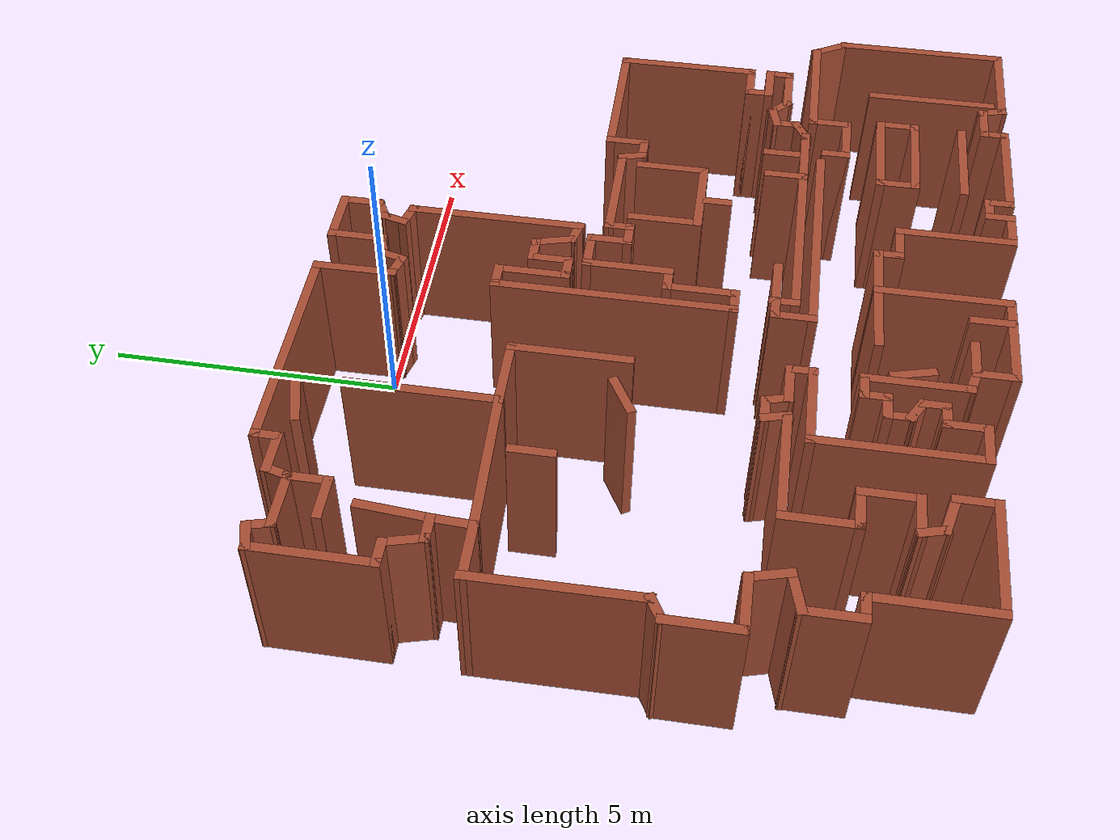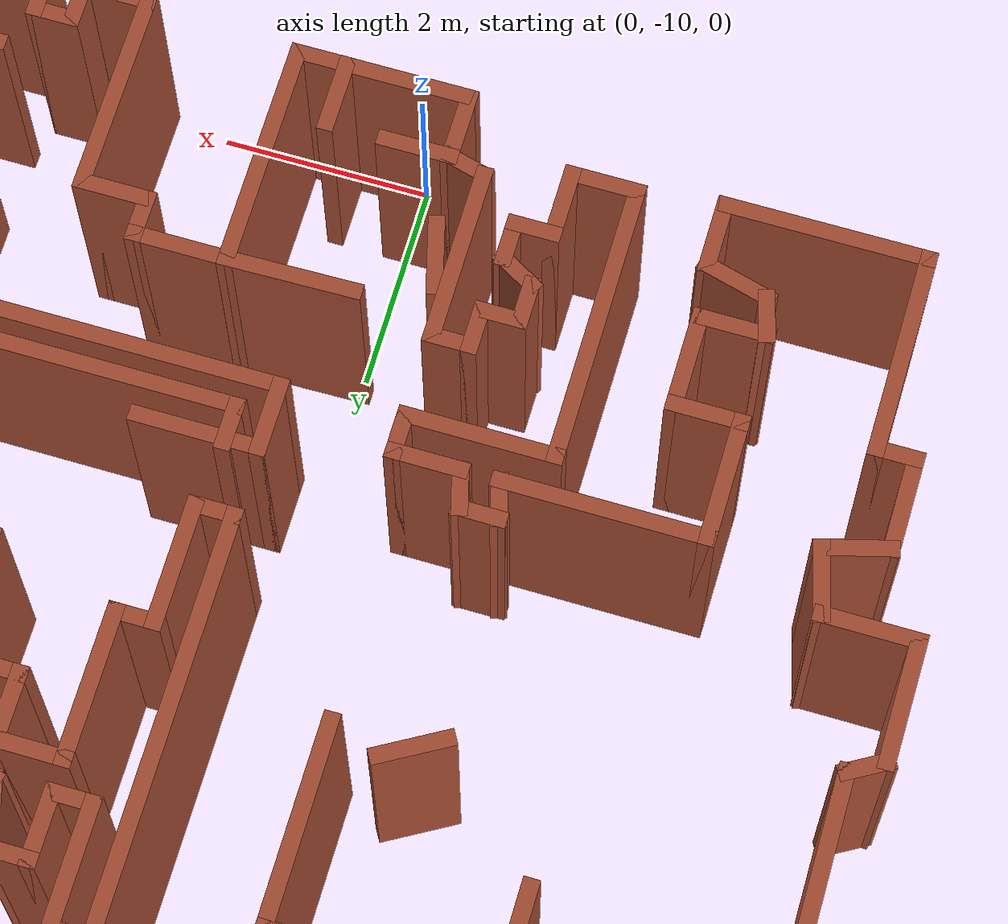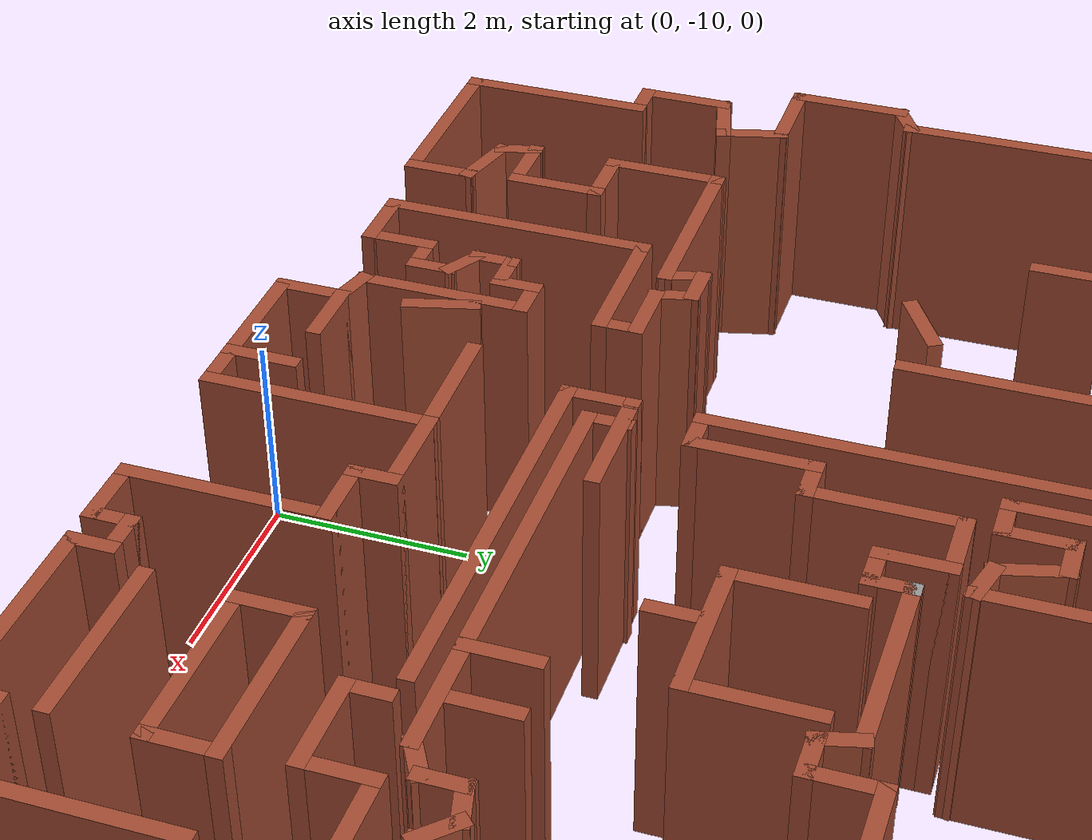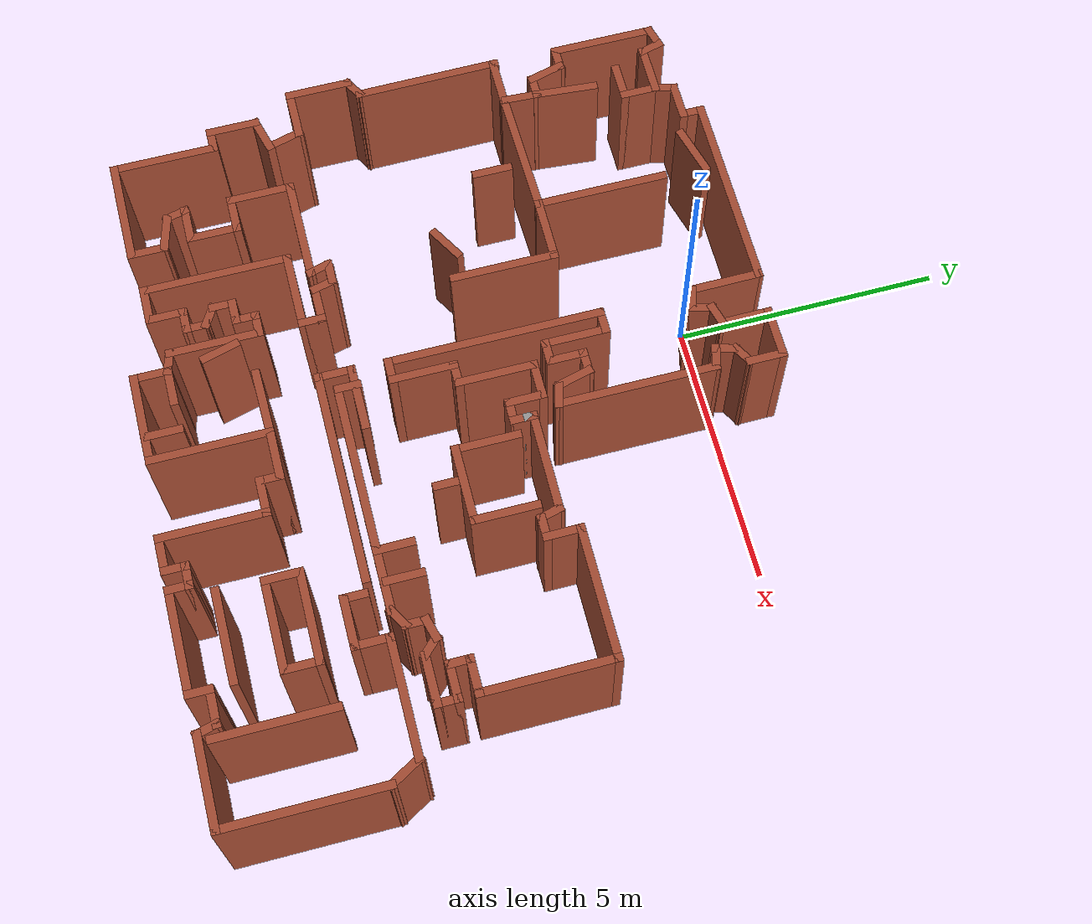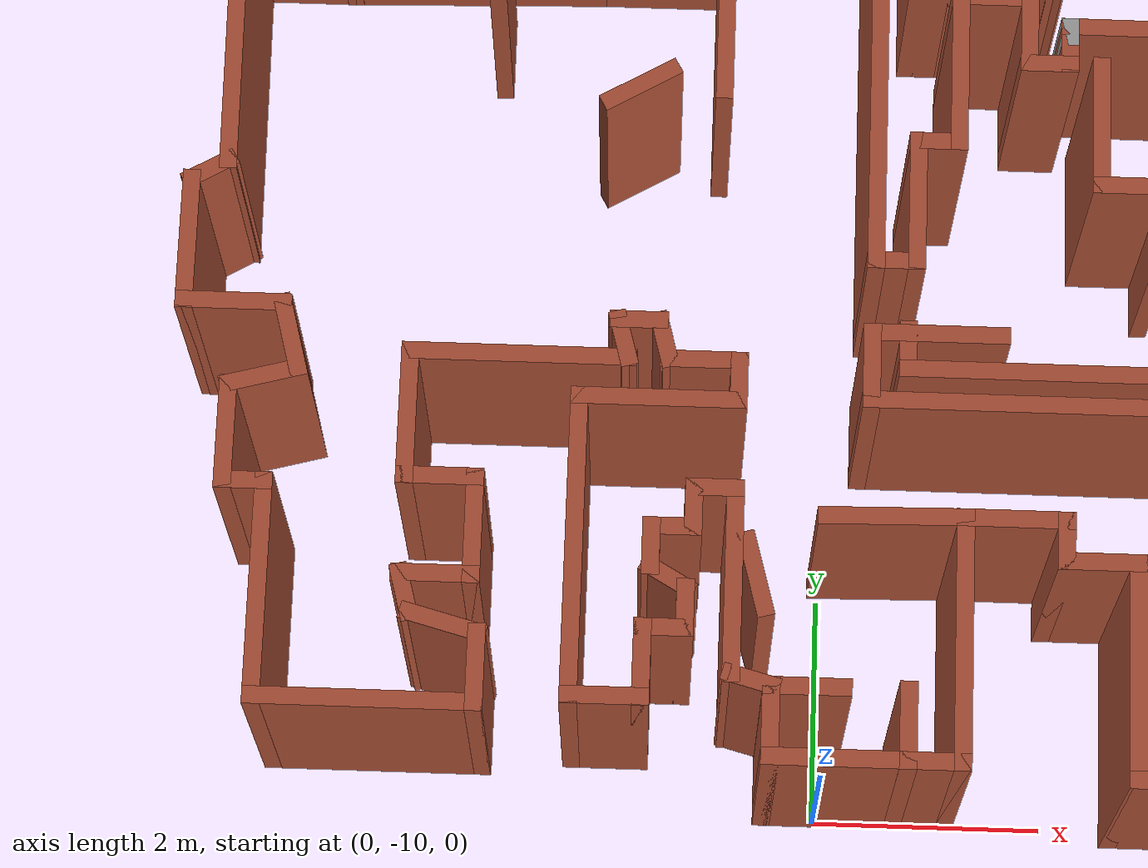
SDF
<?xml version='1.0'?>
<sdf version='1.6'>
  <model name='map_29'>
    <pose frame=''>1.07373 -4.43105 0 0 -0 0</pose>
    <link name='Wall_0'>
      <collision name='Wall_0_Collision'>
        <geometry>
          <box>
            <size>3.75 0.15 2.5</size>
          </box>
        </geometry>
        <pose frame=''>0 0 1.25 0 -0 0</pose>
      </collision>
      <visual name='Wall_0_Visual'>
        <pose frame=''>0 0 1.25 0 -0 0</pose>
        <geometry>
          <box>
            <size>3.75 0.15 2.5</size>
          </box>
        </geometry>
        <material>
          <script>
            <uri>file://media/materials/scripts/gazebo.material</uri>
            <name>Gazebo/Bricks</name>
          </script>
          <ambient>1 1 1 1</ambient>
        </material>
        <meta>
          <layer>0</layer>
        </meta>
      </visual>
      <pose frame=''>-2.54851 5.6282 0 0 -0 3.14159</pose>
    </link>
    <link name='Wall_10'>
      <collision name='Wall_10_Collision'>
        <geometry>
          <box>
            <size>2 0.15 2.5</size>
          </box>
        </geometry>
        <pose frame=''>0 0 1.25 0 -0 0</pose>
      </collision>
      <visual name='Wall_10_Visual'>
        <pose frame=''>0 0 1.25 0 -0 0</pose>
        <geometry>
          <box>
            <size>2 0.15 2.5</size>
          </box>
        </geometry>
        <material>
          <script>
            <uri>file://media/materials/scripts/gazebo.material</uri>
            <name>Gazebo/Bricks</name>
          </script>
          <ambient>1 1 1 1</ambient>
        </material>
        <meta>
          <layer>0</layer>
        </meta>
      </visual>
      <pose frame=''>-6.31776 4.26261 0 0 -0 -1.5708</pose>
    </link>
    <link name='Wall_100'>
      <collision name='Wall_100_Collision'>
        <geometry>
          <box>
            <size>0.75 0.15 2.5</size>
          </box>
        </geometry>
        <pose frame=''>0 0 1.25 0 -0 0</pose>
      </collision>
      <visual name='Wall_100_Visual'>
        <pose frame=''>0 0 1.25 0 -0 0</pose>
        <geometry>
          <box>
            <size>0.75 0.15 2.5</size>
          </box>
        </geometry>
        <material>
          <script>
            <uri>file://media/materials/scripts/gazebo.material</uri>
            <name>Gazebo/Bricks</name>
          </script>
          <ambient>1 1 1 1</ambient>
        </material>
        <meta>
          <layer>0</layer>
        </meta>
      </visual>
      <pose frame=''>6.46557 -2.50228 0 0 -0 2.0944</pose>
    </link>
    <link name='Wall_101'>
      <collision name='Wall_101_Collision'>
        <geometry>
          <box>
            <size>2.25 0.15 2.5</size>
          </box>
        </geometry>
        <pose frame=''>0 0 1.25 0 -0 0</pose>
      </collision>
      <visual name='Wall_101_Visual'>
        <pose frame=''>0 0 1.25 0 -0 0</pose>
        <geometry>
          <box>
            <size>2.25 0.15 2.5</size>
          </box>
        </geometry>
        <material>
          <script>
            <uri>file://media/materials/scripts/gazebo.material</uri>
            <name>Gazebo/Bricks</name>
          </script>
          <ambient>1 1 1 1</ambient>
        </material>
        <meta>
          <layer>0</layer>
        </meta>
      </visual>
      <pose frame=''>5.26557 -2.24247 0 0 -0 3.14159</pose>
    </link>
    <link name='Wall_102'>
      <collision name='Wall_102_Collision'>
        <geometry>
          <box>
            <size>0.75 0.15 2.5</size>
          </box>
        </geometry>
        <pose frame=''>0 0 1.25 0 -0 0</pose>
      </collision>
      <visual name='Wall_102_Visual'>
        <pose frame=''>0 0 1.25 0 -0 0</pose>
        <geometry>
          <box>
            <size>0.75 0.15 2.5</size>
          </box>
        </geometry>
        <material>
          <script>
            <uri>file://media/materials/scripts/gazebo.material</uri>
            <name>Gazebo/Bricks</name>
          </script>
          <ambient>1 1 1 1</ambient>
        </material>
        <meta>
          <layer>0</layer>
        </meta>
      </visual>
      <pose frame=''>4.21557 -2.54247 0 0 -0 -1.5708</pose>
    </link>
    <link name='Wall_103'>
      <collision name='Wall_103_Collision'>
        <geometry>
          <box>
            <size>1 0.15 2.5</size>
          </box>
        </geometry>
        <pose frame=''>0 0 1.25 0 -0 0</pose>
      </collision>
      <visual name='Wall_103_Visual'>
        <pose frame=''>0 0 1.25 0 -0 0</pose>
        <geometry>
          <box>
            <size>1 0.15 2.5</size>
          </box>
        </geometry>
        <material>
          <script>
            <uri>file://media/materials/scripts/gazebo.material</uri>
            <name>Gazebo/Bricks</name>
          </script>
          <ambient>1 1 1 1</ambient>
        </material>
        <meta>
          <layer>0</layer>
        </meta>
      </visual>
      <pose frame=''>3.79057 -2.84247 0 0 -0 3.14159</pose>
    </link>
    <link name='Wall_104'>
      <collision name='Wall_104_Collision'>
        <geometry>
          <box>
            <size>0.5 0.15 2.5</size>
          </box>
        </geometry>
        <pose frame=''>0 0 1.25 0 -0 0</pose>
      </collision>
      <visual name='Wall_104_Visual'>
        <pose frame=''>0 0 1.25 0 -0 0</pose>
        <geometry>
          <box>
            <size>0.5 0.15 2.5</size>
          </box>
        </geometry>
        <material>
          <script>
            <uri>file://media/materials/scripts/gazebo.material</uri>
            <name>Gazebo/Bricks</name>
          </script>
          <ambient>1 1 1 1</ambient>
        </material>
        <meta>
          <layer>0</layer>
        </meta>
      </visual>
      <pose frame=''>3.36557 -2.66747 0 0 -0 1.5708</pose>
    </link>
    <link name='Wall_107'>
      <collision name='Wall_107_Collision'>
        <geometry>
          <box>
            <size>4 0.15 2.5</size>
          </box>
        </geometry>
        <pose frame=''>0 0 1.25 0 -0 0</pose>
      </collision>
      <visual name='Wall_107_Visual'>
        <pose frame=''>0 0 1.25 0 -0 0</pose>
        <geometry>
          <box>
            <size>4 0.15 2.5</size>
          </box>
        </geometry>
        <material>
          <script>
            <uri>file://media/materials/scripts/gazebo.material</uri>
            <name>Gazebo/Bricks</name>
          </script>
          <ambient>1 1 1 1</ambient>
        </material>
        <meta>
          <layer>0</layer>
        </meta>
      </visual>
      <pose frame=''>1.18819 -2.4126 0 0 -0 3.14159</pose>
    </link>
    <link name='Wall_108'>
      <collision name='Wall_108_Collision'>
        <geometry>
          <box>
            <size>0.75 0.15 2.5</size>
          </box>
        </geometry>
        <pose frame=''>0 0 1.25 0 -0 0</pose>
      </collision>
      <visual name='Wall_108_Visual'>
        <pose frame=''>0 0 1.25 0 -0 0</pose>
        <geometry>
          <box>
            <size>0.75 0.15 2.5</size>
          </box>
        </geometry>
        <material>
          <script>
            <uri>file://media/materials/scripts/gazebo.material</uri>
            <name>Gazebo/Bricks</name>
          </script>
          <ambient>1 1 1 1</ambient>
        </material>
        <meta>
          <layer>0</layer>
        </meta>
      </visual>
      <pose frame=''>-0.736808 -2.1126 0 0 -0 1.5708</pose>
    </link>
    <link name='Wall_109'>
      <collision name='Wall_109_Collision'>
        <geometry>
          <box>
            <size>1.25 0.15 2.5</size>
          </box>
        </geometry>
        <pose frame=''>0 0 1.25 0 -0 0</pose>
      </collision>
      <visual name='Wall_109_Visual'>
        <pose frame=''>0 0 1.25 0 -0 0</pose>
        <geometry>
          <box>
            <size>1.25 0.15 2.5</size>
          </box>
        </geometry>
        <material>
          <script>
            <uri>file://media/materials/scripts/gazebo.material</uri>
            <name>Gazebo/Bricks</name>
          </script>
          <ambient>1 1 1 1</ambient>
        </material>
        <meta>
          <layer>0</layer>
        </meta>
      </visual>
      <pose frame=''>-0.186808 -1.8126 0 0 -0 0</pose>
    </link>
    <link name='Wall_11'>
      <collision name='Wall_11_Collision'>
        <geometry>
          <box>
            <size>0.5 0.15 2.5</size>
          </box>
        </geometry>
        <pose frame=''>0 0 1.25 0 -0 0</pose>
      </collision>
      <visual name='Wall_11_Visual'>
        <pose frame=''>0 0 1.25 0 -0 0</pose>
        <geometry>
          <box>
            <size>0.5 0.15 2.5</size>
          </box>
        </geometry>
        <material>
          <script>
            <uri>file://media/materials/scripts/gazebo.material</uri>
            <name>Gazebo/Bricks</name>
          </script>
          <ambient>1 1 1 1</ambient>
        </material>
        <meta>
          <layer>0</layer>
        </meta>
      </visual>
      <pose frame=''>-6.14276 3.33761 0 0 -0 0</pose>
    </link>
    <link name='Wall_111'>
      <collision name='Wall_111_Collision'>
        <geometry>
          <box>
            <size>0.5 0.15 2.5</size>
          </box>
        </geometry>
        <pose frame=''>0 0 1.25 0 -0 0</pose>
      </collision>
      <visual name='Wall_111_Visual'>
        <pose frame=''>0 0 1.25 0 -0 0</pose>
        <geometry>
          <box>
            <size>0.5 0.15 2.5</size>
          </box>
        </geometry>
        <material>
          <script>
            <uri>file://media/materials/scripts/gazebo.material</uri>
            <name>Gazebo/Bricks</name>
          </script>
          <ambient>1 1 1 1</ambient>
        </material>
        <meta>
          <layer>0</layer>
        </meta>
      </visual>
      <pose frame=''>-0.431108 -1.9528 0 0 -0 -1.5708</pose>
    </link>
    <link name='Wall_112'>
      <collision name='Wall_112_Collision'>
        <geometry>
          <box>
            <size>3.25 0.15 2.5</size>
          </box>
        </geometry>
        <pose frame=''>0 0 1.25 0 -0 0</pose>
      </collision>
      <visual name='Wall_112_Visual'>
        <pose frame=''>0 0 1.25 0 -0 0</pose>
        <geometry>
          <box>
            <size>3.25 0.15 2.5</size>
          </box>
        </geometry>
        <material>
          <script>
            <uri>file://media/materials/scripts/gazebo.material</uri>
            <name>Gazebo/Bricks</name>
          </script>
          <ambient>1 1 1 1</ambient>
        </material>
        <meta>
          <layer>0</layer>
        </meta>
      </visual>
      <pose frame=''>1.11889 -2.1278 0 0 -0 0</pose>
    </link>
    <link name='Wall_113'>
      <collision name='Wall_113_Collision'>
        <geometry>
          <box>
            <size>0.75 0.15 2.5</size>
          </box>
        </geometry>
        <pose frame=''>0 0 1.25 0 -0 0</pose>
      </collision>
      <visual name='Wall_113_Visual'>
        <pose frame=''>0 0 1.25 0 -0 0</pose>
        <geometry>
          <box>
            <size>0.75 0.15 2.5</size>
          </box>
        </geometry>
        <material>
          <script>
            <uri>file://media/materials/scripts/gazebo.material</uri>
            <name>Gazebo/Bricks</name>
          </script>
          <ambient>1 1 1 1</ambient>
        </material>
        <meta>
          <layer>0</layer>
        </meta>
      </visual>
      <pose frame=''>2.66889 -1.8278 0 0 -0 1.5708</pose>
    </link>
    <link name='Wall_115'>
      <collision name='Wall_115_Collision'>
        <geometry>
          <box>
            <size>1.25 0.15 2.5</size>
          </box>
        </geometry>
        <pose frame=''>0 0 1.25 0 -0 0</pose>
      </collision>
      <visual name='Wall_115_Visual'>
        <pose frame=''>0 0 1.25 0 -0 0</pose>
        <geometry>
          <box>
            <size>1.25 0.15 2.5</size>
          </box>
        </geometry>
        <material>
          <script>
            <uri>file://media/materials/scripts/gazebo.material</uri>
            <name>Gazebo/Bricks</name>
          </script>
          <ambient>1 1 1 1</ambient>
        </material>
        <meta>
          <layer>0</layer>
        </meta>
      </visual>
      <pose frame=''>3.21889 -2.1278 0 0 -0 0</pose>
    </link>
    <link name='Wall_116'>
      <collision name='Wall_116_Collision'>
        <geometry>
          <box>
            <size>0.5 0.15 2.5</size>
          </box>
        </geometry>
        <pose frame=''>0 0 1.25 0 -0 0</pose>
      </collision>
      <visual name='Wall_116_Visual'>
        <pose frame=''>0 0 1.25 0 -0 0</pose>
        <geometry>
          <box>
            <size>0.5 0.15 2.5</size>
          </box>
        </geometry>
        <material>
          <script>
            <uri>file://media/materials/scripts/gazebo.material</uri>
            <name>Gazebo/Bricks</name>
          </script>
          <ambient>1 1 1 1</ambient>
        </material>
        <meta>
          <layer>0</layer>
        </meta>
      </visual>
      <pose frame=''>3.92045 -2.0403 0 0 -0 0.523599</pose>
    </link>
    <link name='Wall_117'>
      <collision name='Wall_117_Collision'>
        <geometry>
          <box>
            <size>0.5 0.15 2.5</size>
          </box>
        </geometry>
        <pose frame=''>0 0 1.25 0 -0 0</pose>
      </collision>
      <visual name='Wall_117_Visual'>
        <pose frame=''>0 0 1.25 0 -0 0</pose>
        <geometry>
          <box>
            <size>0.5 0.15 2.5</size>
          </box>
        </geometry>
        <material>
          <script>
            <uri>file://media/materials/scripts/gazebo.material</uri>
            <name>Gazebo/Bricks</name>
          </script>
          <ambient>1 1 1 1</ambient>
        </material>
        <meta>
          <layer>0</layer>
        </meta>
      </visual>
      <pose frame=''>4.072 -1.7778 0 0 -0 1.5708</pose>
    </link>
    <link name='Wall_118'>
      <collision name='Wall_118_Collision'>
        <geometry>
          <box>
            <size>0.5 0.15 2.5</size>
          </box>
        </geometry>
        <pose frame=''>0 0 1.25 0 -0 0</pose>
      </collision>
      <visual name='Wall_118_Visual'>
        <pose frame=''>0 0 1.25 0 -0 0</pose>
        <geometry>
          <box>
            <size>0.5 0.15 2.5</size>
          </box>
        </geometry>
        <material>
          <script>
            <uri>file://media/materials/scripts/gazebo.material</uri>
            <name>Gazebo/Bricks</name>
          </script>
          <ambient>1 1 1 1</ambient>
        </material>
        <meta>
          <layer>0</layer>
        </meta>
      </visual>
      <pose frame=''>4.24104 -1.55751 0 0 -0 0.261799</pose>
    </link>
    <link name='Wall_119'>
      <collision name='Wall_119_Collision'>
        <geometry>
          <box>
            <size>0.5 0.15 2.5</size>
          </box>
        </geometry>
        <pose frame=''>0 0 1.25 0 -0 0</pose>
      </collision>
      <visual name='Wall_119_Visual'>
        <pose frame=''>0 0 1.25 0 -0 0</pose>
        <geometry>
          <box>
            <size>0.5 0.15 2.5</size>
          </box>
        </geometry>
        <material>
          <script>
            <uri>file://media/materials/scripts/gazebo.material</uri>
            <name>Gazebo/Bricks</name>
          </script>
          <ambient>1 1 1 1</ambient>
        </material>
        <meta>
          <layer>0</layer>
        </meta>
      </visual>
      <pose frame=''>4.53382 -1.63596 0 0 -0 -0.785398</pose>
    </link>
    <link name='Wall_120'>
      <collision name='Wall_120_Collision'>
        <geometry>
          <box>
            <size>1 0.15 2.5</size>
          </box>
        </geometry>
        <pose frame=''>0 0 1.25 0 -0 0</pose>
      </collision>
      <visual name='Wall_120_Visual'>
        <pose frame=''>0 0 1.25 0 -0 0</pose>
        <geometry>
          <box>
            <size>1 0.15 2.5</size>
          </box>
        </geometry>
        <material>
          <script>
            <uri>file://media/materials/scripts/gazebo.material</uri>
            <name>Gazebo/Bricks</name>
          </script>
          <ambient>1 1 1 1</ambient>
        </material>
        <meta>
          <layer>0</layer>
        </meta>
      </visual>
      <pose frame=''>5.08256 -1.7597 0 0 -0 0</pose>
    </link>
    <link name='Wall_125'>
      <collision name='Wall_125_Collision'>
        <geometry>
          <box>
            <size>0.5 0.15 2.5</size>
          </box>
        </geometry>
        <pose frame=''>0 0 1.25 0 -0 0</pose>
      </collision>
      <visual name='Wall_125_Visual'>
        <pose frame=''>0 0 1.25 0 -0 0</pose>
        <geometry>
          <box>
            <size>0.5 0.15 2.5</size>
          </box>
        </geometry>
        <material>
          <script>
            <uri>file://media/materials/scripts/gazebo.material</uri>
            <name>Gazebo/Bricks</name>
          </script>
          <ambient>1 1 1 1</ambient>
        </material>
        <meta>
          <layer>0</layer>
        </meta>
      </visual>
      <pose frame=''>5.50756 -1.5847 0 0 -0 1.5708</pose>
    </link>
    <link name='Wall_126'>
      <collision name='Wall_126_Collision'>
        <geometry>
          <box>
            <size>0.75 0.15 2.5</size>
          </box>
        </geometry>
        <pose frame=''>0 0 1.25 0 -0 0</pose>
      </collision>
      <visual name='Wall_126_Visual'>
        <pose frame=''>0 0 1.25 0 -0 0</pose>
        <geometry>
          <box>
            <size>0.75 0.15 2.5</size>
          </box>
        </geometry>
        <material>
          <script>
            <uri>file://media/materials/scripts/gazebo.material</uri>
            <name>Gazebo/Bricks</name>
          </script>
          <ambient>1 1 1 1</ambient>
        </material>
        <meta>
          <layer>0</layer>
        </meta>
      </visual>
      <pose frame=''>5.20756 -1.4097 0 0 -0 3.14159</pose>
    </link>
    <link name='Wall_127'>
      <collision name='Wall_127_Collision'>
        <geometry>
          <box>
            <size>0.5 0.15 2.5</size>
          </box>
        </geometry>
        <pose frame=''>0 0 1.25 0 -0 0</pose>
      </collision>
      <visual name='Wall_127_Visual'>
        <pose frame=''>0 0 1.25 0 -0 0</pose>
        <geometry>
          <box>
            <size>0.5 0.15 2.5</size>
          </box>
        </geometry>
        <material>
          <script>
            <uri>file://media/materials/scripts/gazebo.material</uri>
            <name>Gazebo/Bricks</name>
          </script>
          <ambient>1 1 1 1</ambient>
        </material>
        <meta>
          <layer>0</layer>
        </meta>
      </visual>
      <pose frame=''>4.90756 -1.2347 0 0 -0 1.5708</pose>
    </link>
    <link name='Wall_128'>
      <collision name='Wall_128_Collision'>
        <geometry>
          <box>
            <size>0.75 0.15 2.5</size>
          </box>
        </geometry>
        <pose frame=''>0 0 1.25 0 -0 0</pose>
      </collision>
      <visual name='Wall_128_Visual'>
        <pose frame=''>0 0 1.25 0 -0 0</pose>
        <geometry>
          <box>
            <size>0.75 0.15 2.5</size>
          </box>
        </geometry>
        <material>
          <script>
            <uri>file://media/materials/scripts/gazebo.material</uri>
            <name>Gazebo/Bricks</name>
          </script>
          <ambient>1 1 1 1</ambient>
        </material>
        <meta>
          <layer>0</layer>
        </meta>
      </visual>
      <pose frame=''>5.20756 -1.0597 0 0 -0 0</pose>
    </link>
    <link name='Wall_129'>
      <collision name='Wall_129_Collision'>
        <geometry>
          <box>
            <size>2.5 0.15 2.5</size>
          </box>
        </geometry>
        <pose frame=''>0 0 1.25 0 -0 0</pose>
      </collision>
      <visual name='Wall_129_Visual'>
        <pose frame=''>0 0 1.25 0 -0 0</pose>
        <geometry>
          <box>
            <size>2.5 0.15 2.5</size>
          </box>
        </geometry>
        <material>
          <script>
            <uri>file://media/materials/scripts/gazebo.material</uri>
            <name>Gazebo/Bricks</name>
          </script>
          <ambient>1 1 1 1</ambient>
        </material>
        <meta>
          <layer>0</layer>
        </meta>
      </visual>
      <pose frame=''>5.50756 0.115297 0 0 -0 1.5708</pose>
    </link>
    <link name='Wall_130'>
      <collision name='Wall_130_Collision'>
        <geometry>
          <box>
            <size>2.5 0.15 2.5</size>
          </box>
        </geometry>
        <pose frame=''>0 0 1.25 0 -0 0</pose>
      </collision>
      <visual name='Wall_130_Visual'>
        <pose frame=''>0 0 1.25 0 -0 0</pose>
        <geometry>
          <box>
            <size>2.5 0.15 2.5</size>
          </box>
        </geometry>
        <material>
          <script>
            <uri>file://media/materials/scripts/gazebo.material</uri>
            <name>Gazebo/Bricks</name>
          </script>
          <ambient>1 1 1 1</ambient>
        </material>
        <meta>
          <layer>0</layer>
        </meta>
      </visual>
      <pose frame=''>4.33256 1.2903 0 0 -0 3.14159</pose>
    </link>
    <link name='Wall_135'>
      <collision name='Wall_135_Collision'>
        <geometry>
          <box>
            <size>0.25 0.15 2.5</size>
          </box>
        </geometry>
        <pose frame=''>0 0 1.25 0 -0 0</pose>
      </collision>
      <visual name='Wall_135_Visual'>
        <pose frame=''>0 0 1.25 0 -0 0</pose>
        <geometry>
          <box>
            <size>0.25 0.15 2.5</size>
          </box>
        </geometry>
        <material>
          <script>
            <uri>file://media/materials/scripts/gazebo.material</uri>
            <name>Gazebo/Grey</name>
          </script>
          <ambient>1 1 1 1</ambient>
        </material>
        <meta>
          <layer>0</layer>
        </meta>
      </visual>
      <pose frame=''>0.931681 0.98689 0 0 -0 -1.5708</pose>
    </link>
    <link name='Wall_139'>
      <collision name='Wall_139_Collision'>
        <geometry>
          <box>
            <size>0.75 0.15 2.5</size>
          </box>
        </geometry>
        <pose frame=''>0 0 1.25 0 -0 0</pose>
      </collision>
      <visual name='Wall_139_Visual'>
        <pose frame=''>0 0 1.25 0 -0 0</pose>
        <geometry>
          <box>
            <size>0.75 0.15 2.5</size>
          </box>
        </geometry>
        <material>
          <script>
            <uri>file://media/materials/scripts/gazebo.material</uri>
            <name>Gazebo/Bricks</name>
          </script>
          <ambient>1 1 1 1</ambient>
        </material>
        <meta>
          <layer>0</layer>
        </meta>
      </visual>
      <pose frame=''>3.15756 0.990297 0 0 -0 -1.5708</pose>
    </link>
    <link name='Wall_140'>
      <collision name='Wall_140_Collision'>
        <geometry>
          <box>
            <size>0.5 0.15 2.5</size>
          </box>
        </geometry>
        <pose frame=''>0 0 1.25 0 -0 0</pose>
      </collision>
      <visual name='Wall_140_Visual'>
        <pose frame=''>0 0 1.25 0 -0 0</pose>
        <geometry>
          <box>
            <size>0.5 0.15 2.5</size>
          </box>
        </geometry>
        <material>
          <script>
            <uri>file://media/materials/scripts/gazebo.material</uri>
            <name>Gazebo/Bricks</name>
          </script>
          <ambient>1 1 1 1</ambient>
        </material>
        <meta>
          <layer>0</layer>
        </meta>
      </visual>
      <pose frame=''>2.98256 0.690297 0 0 -0 3.14159</pose>
    </link>
    <link name='Wall_141'>
      <collision name='Wall_141_Collision'>
        <geometry>
          <box>
            <size>0.5 0.15 2.5</size>
          </box>
        </geometry>
        <pose frame=''>0 0 1.25 0 -0 0</pose>
      </collision>
      <visual name='Wall_141_Visual'>
        <pose frame=''>0 0 1.25 0 -0 0</pose>
        <geometry>
          <box>
            <size>0.5 0.15 2.5</size>
          </box>
        </geometry>
        <material>
          <script>
            <uri>file://media/materials/scripts/gazebo.material</uri>
            <name>Gazebo/Bricks</name>
          </script>
          <ambient>1 1 1 1</ambient>
        </material>
        <meta>
          <layer>0</layer>
        </meta>
      </visual>
      <pose frame=''>2.76227 0.859334 0 0 -0 1.8326</pose>
    </link>
    <link name='Wall_142'>
      <collision name='Wall_142_Collision'>
        <geometry>
          <box>
            <size>1.93532 0.15 2.5</size>
          </box>
        </geometry>
        <pose frame=''>0 0 1.25 0 -0 0</pose>
      </collision>
      <visual name='Wall_142_Visual'>
        <pose frame=''>0 0 1.25 0 -0 0</pose>
        <geometry>
          <box>
            <size>1.93532 0.15 2.5</size>
          </box>
        </geometry>
        <material>
          <script>
            <uri>file://media/materials/scripts/gazebo.material</uri>
            <name>Gazebo/Bricks</name>
          </script>
          <ambient>1 1 1 1</ambient>
        </material>
        <meta>
          <layer>0</layer>
        </meta>
      </visual>
      <pose frame=''>1.82433 1.03263 0 0 -0 3.13682</pose>
    </link>
    <link name='Wall_145'>
      <collision name='Wall_145_Collision'>
        <geometry>
          <box>
            <size>0.5 0.15 2.5</size>
          </box>
        </geometry>
        <pose frame=''>0 0 1.25 0 -0 0</pose>
      </collision>
      <visual name='Wall_145_Visual'>
        <pose frame=''>0 0 1.25 0 -0 0</pose>
        <geometry>
          <box>
            <size>0.5 0.15 2.5</size>
          </box>
        </geometry>
        <material>
          <script>
            <uri>file://media/materials/scripts/gazebo.material</uri>
            <name>Gazebo/Bricks</name>
          </script>
          <ambient>1 1 1 1</ambient>
        </material>
        <meta>
          <layer>0</layer>
        </meta>
      </visual>
      <pose frame=''>0.931681 0.86189 0 0 -0 -1.5708</pose>
    </link>
    <link name='Wall_146'>
      <collision name='Wall_146_Collision'>
        <geometry>
          <box>
            <size>0.5 0.15 2.5</size>
          </box>
        </geometry>
        <pose frame=''>0 0 1.25 0 -0 0</pose>
      </collision>
      <visual name='Wall_146_Visual'>
        <pose frame=''>0 0 1.25 0 -0 0</pose>
        <geometry>
          <box>
            <size>0.5 0.15 2.5</size>
          </box>
        </geometry>
        <material>
          <script>
            <uri>file://media/materials/scripts/gazebo.material</uri>
            <name>Gazebo/Bricks</name>
          </script>
          <ambient>1 1 1 1</ambient>
        </material>
        <meta>
          <layer>0</layer>
        </meta>
      </visual>
      <pose frame=''>0.756681 0.686889 0 0 -0 3.14159</pose>
    </link>
    <link name='Wall_149'>
      <collision name='Wall_149_Collision'>
        <geometry>
          <box>
            <size>0.75 0.15 2.5</size>
          </box>
        </geometry>
        <pose frame=''>0 0 1.25 0 -0 0</pose>
      </collision>
      <visual name='Wall_149_Visual'>
        <pose frame=''>0 0 1.25 0 -0 0</pose>
        <geometry>
          <box>
            <size>0.75 0.15 2.5</size>
          </box>
        </geometry>
        <material>
          <script>
            <uri>file://media/materials/scripts/gazebo.material</uri>
            <name>Gazebo/Bricks</name>
          </script>
          <ambient>1 1 1 1</ambient>
        </material>
        <meta>
          <layer>0</layer>
        </meta>
      </visual>
      <pose frame=''>0.581681 0.98689 0 0 -0 1.5708</pose>
    </link>
    <link name='Wall_15'>
      <collision name='Wall_15_Collision'>
        <geometry>
          <box>
            <size>0.75 0.15 2.5</size>
          </box>
        </geometry>
        <pose frame=''>0 0 1.25 0 -0 0</pose>
      </collision>
      <visual name='Wall_15_Visual'>
        <pose frame=''>0 0 1.25 0 -0 0</pose>
        <geometry>
          <box>
            <size>0.75 0.15 2.5</size>
          </box>
        </geometry>
        <material>
          <script>
            <uri>file://media/materials/scripts/gazebo.material</uri>
            <name>Gazebo/Bricks</name>
          </script>
          <ambient>1 1 1 1</ambient>
        </material>
        <meta>
          <layer>0</layer>
        </meta>
      </visual>
      <pose frame=''>-5.89011 3.04783 0 0 -0 -1.309</pose>
    </link>
    <link name='Wall_150'>
      <collision name='Wall_150_Collision'>
        <geometry>
          <box>
            <size>0.75 0.15 2.5</size>
          </box>
        </geometry>
        <pose frame=''>0 0 1.25 0 -0 0</pose>
      </collision>
      <visual name='Wall_150_Visual'>
        <pose frame=''>0 0 1.25 0 -0 0</pose>
        <geometry>
          <box>
            <size>0.75 0.15 2.5</size>
          </box>
        </geometry>
        <material>
          <script>
            <uri>file://media/materials/scripts/gazebo.material</uri>
            <name>Gazebo/Bricks</name>
          </script>
          <ambient>1 1 1 1</ambient>
        </material>
        <meta>
          <layer>0</layer>
        </meta>
      </visual>
      <pose frame=''>0.281681 1.28689 0 0 -0 3.14159</pose>
    </link>
    <link name='Wall_151'>
      <collision name='Wall_151_Collision'>
        <geometry>
          <box>
            <size>1.5 0.15 2.5</size>
          </box>
        </geometry>
        <pose frame=''>0 0 1.25 0 -0 0</pose>
      </collision>
      <visual name='Wall_151_Visual'>
        <pose frame=''>0 0 1.25 0 -0 0</pose>
        <geometry>
          <box>
            <size>1.5 0.15 2.5</size>
          </box>
        </geometry>
        <material>
          <script>
            <uri>file://media/materials/scripts/gazebo.material</uri>
            <name>Gazebo/Bricks</name>
          </script>
          <ambient>1 1 1 1</ambient>
        </material>
        <meta>
          <layer>0</layer>
        </meta>
      </visual>
      <pose frame=''>-0.018319 0.61189 0 0 -0 -1.5708</pose>
    </link>
    <link name='Wall_152'>
      <collision name='Wall_152_Collision'>
        <geometry>
          <box>
            <size>0.5 0.15 2.5</size>
          </box>
        </geometry>
        <pose frame=''>0 0 1.25 0 -0 0</pose>
      </collision>
      <visual name='Wall_152_Visual'>
        <pose frame=''>0 0 1.25 0 -0 0</pose>
        <geometry>
          <box>
            <size>0.5 0.15 2.5</size>
          </box>
        </geometry>
        <material>
          <script>
            <uri>file://media/materials/scripts/gazebo.material</uri>
            <name>Gazebo/Bricks</name>
          </script>
          <ambient>1 1 1 1</ambient>
        </material>
        <meta>
          <layer>0</layer>
        </meta>
      </visual>
      <pose frame=''>-0.193319 -0.06311 0 0 -0 3.14159</pose>
    </link>
    <link name='Wall_153'>
      <collision name='Wall_153_Collision'>
        <geometry>
          <box>
            <size>1.25 0.15 2.5</size>
          </box>
        </geometry>
        <pose frame=''>0 0 1.25 0 -0 0</pose>
      </collision>
      <visual name='Wall_153_Visual'>
        <pose frame=''>0 0 1.25 0 -0 0</pose>
        <geometry>
          <box>
            <size>1.25 0.15 2.5</size>
          </box>
        </geometry>
        <material>
          <script>
            <uri>file://media/materials/scripts/gazebo.material</uri>
            <name>Gazebo/Bricks</name>
          </script>
          <ambient>1 1 1 1</ambient>
        </material>
        <meta>
          <layer>0</layer>
        </meta>
      </visual>
      <pose frame=''>-0.368319 -0.613111 0 0 -0 -1.5708</pose>
    </link>
    <link name='Wall_154'>
      <collision name='Wall_154_Collision'>
        <geometry>
          <box>
            <size>0.5 0.15 2.5</size>
          </box>
        </geometry>
        <pose frame=''>0 0 1.25 0 -0 0</pose>
      </collision>
      <visual name='Wall_154_Visual'>
        <pose frame=''>0 0 1.25 0 -0 0</pose>
        <geometry>
          <box>
            <size>0.5 0.15 2.5</size>
          </box>
        </geometry>
        <material>
          <script>
            <uri>file://media/materials/scripts/gazebo.material</uri>
            <name>Gazebo/Bricks</name>
          </script>
          <ambient>1 1 1 1</ambient>
        </material>
        <meta>
          <layer>0</layer>
        </meta>
      </visual>
      <pose frame=''>-0.543319 -1.16311 0 0 -0 3.14159</pose>
    </link>
    <link name='Wall_155'>
      <collision name='Wall_155_Collision'>
        <geometry>
          <box>
            <size>4 0.15 2.5</size>
          </box>
        </geometry>
        <pose frame=''>0 0 1.25 0 -0 0</pose>
      </collision>
      <visual name='Wall_155_Visual'>
        <pose frame=''>0 0 1.25 0 -0 0</pose>
        <geometry>
          <box>
            <size>4 0.15 2.5</size>
          </box>
        </geometry>
        <material>
          <script>
            <uri>file://media/materials/scripts/gazebo.material</uri>
            <name>Gazebo/Bricks</name>
          </script>
          <ambient>1 1 1 1</ambient>
        </material>
        <meta>
          <layer>0</layer>
        </meta>
      </visual>
      <pose frame=''>-0.718319 0.761889 0 0 -0 1.5708</pose>
    </link>
    <link name='Wall_156'>
      <collision name='Wall_156_Collision'>
        <geometry>
          <box>
            <size>0.5 0.15 2.5</size>
          </box>
        </geometry>
        <pose frame=''>0 0 1.25 0 -0 0</pose>
      </collision>
      <visual name='Wall_156_Visual'>
        <pose frame=''>0 0 1.25 0 -0 0</pose>
        <geometry>
          <box>
            <size>0.5 0.15 2.5</size>
          </box>
        </geometry>
        <material>
          <script>
            <uri>file://media/materials/scripts/gazebo.material</uri>
            <name>Gazebo/Bricks</name>
          </script>
          <ambient>1 1 1 1</ambient>
        </material>
        <meta>
          <layer>0</layer>
        </meta>
      </visual>
      <pose frame=''>-0.543319 2.68689 0 0 -0 0</pose>
    </link>
    <link name='Wall_157'>
      <collision name='Wall_157_Collision'>
        <geometry>
          <box>
            <size>1.25 0.15 2.5</size>
          </box>
        </geometry>
        <pose frame=''>0 0 1.25 0 -0 0</pose>
      </collision>
      <visual name='Wall_157_Visual'>
        <pose frame=''>0 0 1.25 0 -0 0</pose>
        <geometry>
          <box>
            <size>1.25 0.15 2.5</size>
          </box>
        </geometry>
        <material>
          <script>
            <uri>file://media/materials/scripts/gazebo.material</uri>
            <name>Gazebo/Bricks</name>
          </script>
          <ambient>1 1 1 1</ambient>
        </material>
        <meta>
          <layer>0</layer>
        </meta>
      </visual>
      <pose frame=''>-0.368319 2.13689 0 0 -0 -1.5708</pose>
    </link>
    <link name='Wall_158'>
      <collision name='Wall_158_Collision'>
        <geometry>
          <box>
            <size>0.5 0.15 2.5</size>
          </box>
        </geometry>
        <pose frame=''>0 0 1.25 0 -0 0</pose>
      </collision>
      <visual name='Wall_158_Visual'>
        <pose frame=''>0 0 1.25 0 -0 0</pose>
        <geometry>
          <box>
            <size>0.5 0.15 2.5</size>
          </box>
        </geometry>
        <material>
          <script>
            <uri>file://media/materials/scripts/gazebo.material</uri>
            <name>Gazebo/Bricks</name>
          </script>
          <ambient>1 1 1 1</ambient>
        </material>
        <meta>
          <layer>0</layer>
        </meta>
      </visual>
      <pose frame=''>-0.193319 1.58689 0 0 -0 0</pose>
    </link>
    <link name='Wall_159'>
      <collision name='Wall_159_Collision'>
        <geometry>
          <box>
            <size>0.75 0.15 2.5</size>
          </box>
        </geometry>
        <pose frame=''>0 0 1.25 0 -0 0</pose>
      </collision>
      <visual name='Wall_159_Visual'>
        <pose frame=''>0 0 1.25 0 -0 0</pose>
        <geometry>
          <box>
            <size>0.75 0.15 2.5</size>
          </box>
        </geometry>
        <material>
          <script>
            <uri>file://media/materials/scripts/gazebo.material</uri>
            <name>Gazebo/Bricks</name>
          </script>
          <ambient>1 1 1 1</ambient>
        </material>
        <meta>
          <layer>0</layer>
        </meta>
      </visual>
      <pose frame=''>-0.018319 1.88689 0 0 -0 1.5708</pose>
    </link>
    <link name='Wall_16'>
      <collision name='Wall_16_Collision'>
        <geometry>
          <box>
            <size>0.5 0.15 2.5</size>
          </box>
        </geometry>
        <pose frame=''>0 0 1.25 0 -0 0</pose>
      </collision>
      <visual name='Wall_16_Visual'>
        <pose frame=''>0 0 1.25 0 -0 0</pose>
        <geometry>
          <box>
            <size>0.5 0.15 2.5</size>
          </box>
        </geometry>
        <material>
          <script>
            <uri>file://media/materials/scripts/gazebo.material</uri>
            <name>Gazebo/Bricks</name>
          </script>
          <ambient>1 1 1 1</ambient>
        </material>
        <meta>
          <layer>0</layer>
        </meta>
      </visual>
      <pose frame=''>-5.63746 2.75806 0 0 -0 0</pose>
    </link>
    <link name='Wall_160'>
      <collision name='Wall_160_Collision'>
        <geometry>
          <box>
            <size>0.5 0.15 2.5</size>
          </box>
        </geometry>
        <pose frame=''>0 0 1.25 0 -0 0</pose>
      </collision>
      <visual name='Wall_160_Visual'>
        <pose frame=''>0 0 1.25 0 -0 0</pose>
        <geometry>
          <box>
            <size>0.5 0.15 2.5</size>
          </box>
        </geometry>
        <material>
          <script>
            <uri>file://media/materials/scripts/gazebo.material</uri>
            <name>Gazebo/Bricks</name>
          </script>
          <ambient>1 1 1 1</ambient>
        </material>
        <meta>
          <layer>0</layer>
        </meta>
      </visual>
      <pose frame=''>0.156681 2.18689 0 0 -0 0</pose>
    </link>
    <link name='Wall_161'>
      <collision name='Wall_161_Collision'>
        <geometry>
          <box>
            <size>0.75 0.15 2.5</size>
          </box>
        </geometry>
        <pose frame=''>0 0 1.25 0 -0 0</pose>
      </collision>
      <visual name='Wall_161_Visual'>
        <pose frame=''>0 0 1.25 0 -0 0</pose>
        <geometry>
          <box>
            <size>0.75 0.15 2.5</size>
          </box>
        </geometry>
        <material>
          <script>
            <uri>file://media/materials/scripts/gazebo.material</uri>
            <name>Gazebo/Bricks</name>
          </script>
          <ambient>1 1 1 1</ambient>
        </material>
        <meta>
          <layer>0</layer>
        </meta>
      </visual>
      <pose frame=''>0.409326 1.89711 0 0 -0 -1.309</pose>
    </link>
    <link name='Wall_162'>
      <collision name='Wall_162_Collision'>
        <geometry>
          <box>
            <size>0.5 0.15 2.5</size>
          </box>
        </geometry>
        <pose frame=''>0 0 1.25 0 -0 0</pose>
      </collision>
      <visual name='Wall_162_Visual'>
        <pose frame=''>0 0 1.25 0 -0 0</pose>
        <geometry>
          <box>
            <size>0.5 0.15 2.5</size>
          </box>
        </geometry>
        <material>
          <script>
            <uri>file://media/materials/scripts/gazebo.material</uri>
            <name>Gazebo/Bricks</name>
          </script>
          <ambient>1 1 1 1</ambient>
        </material>
        <meta>
          <layer>0</layer>
        </meta>
      </visual>
      <pose frame=''>0.656009 1.56204 0 0 -0 -0.261799</pose>
    </link>
    <link name='Wall_165'>
      <collision name='Wall_165_Collision'>
        <geometry>
          <box>
            <size>3 0.15 2.5</size>
          </box>
        </geometry>
        <pose frame=''>0 0 1.25 0 -0 0</pose>
      </collision>
      <visual name='Wall_165_Visual'>
        <pose frame=''>0 0 1.25 0 -0 0</pose>
        <geometry>
          <box>
            <size>3 0.15 2.5</size>
          </box>
        </geometry>
        <material>
          <script>
            <uri>file://media/materials/scripts/gazebo.material</uri>
            <name>Gazebo/Bricks</name>
          </script>
          <ambient>1 1 1 1</ambient>
        </material>
        <meta>
          <layer>0</layer>
        </meta>
      </visual>
      <pose frame=''>0.825046 2.94175 0 0 -0 1.5708</pose>
    </link>
    <link name='Wall_166'>
      <collision name='Wall_166_Collision'>
        <geometry>
          <box>
            <size>0.5 0.15 2.5</size>
          </box>
        </geometry>
        <pose frame=''>0 0 1.25 0 -0 0</pose>
      </collision>
      <visual name='Wall_166_Visual'>
        <pose frame=''>0 0 1.25 0 -0 0</pose>
        <geometry>
          <box>
            <size>0.5 0.15 2.5</size>
          </box>
        </geometry>
        <material>
          <script>
            <uri>file://media/materials/scripts/gazebo.material</uri>
            <name>Gazebo/Bricks</name>
          </script>
          <ambient>1 1 1 1</ambient>
        </material>
        <meta>
          <layer>0</layer>
        </meta>
      </visual>
      <pose frame=''>0.656009 4.41204 0 0 -0 2.87979</pose>
    </link>
    <link name='Wall_167'>
      <collision name='Wall_167_Collision'>
        <geometry>
          <box>
            <size>0.5 0.15 2.5</size>
          </box>
        </geometry>
        <pose frame=''>0 0 1.25 0 -0 0</pose>
      </collision>
      <visual name='Wall_167_Visual'>
        <pose frame=''>0 0 1.25 0 -0 0</pose>
        <geometry>
          <box>
            <size>0.5 0.15 2.5</size>
          </box>
        </geometry>
        <material>
          <script>
            <uri>file://media/materials/scripts/gazebo.material</uri>
            <name>Gazebo/Bricks</name>
          </script>
          <ambient>1 1 1 1</ambient>
        </material>
        <meta>
          <layer>0</layer>
        </meta>
      </visual>
      <pose frame=''>0.532265 4.62637 0 0 -0 1.309</pose>
    </link>
    <link name='Wall_168'>
      <collision name='Wall_168_Collision'>
        <geometry>
          <box>
            <size>0.5 0.15 2.5</size>
          </box>
        </geometry>
        <pose frame=''>0 0 1.25 0 -0 0</pose>
      </collision>
      <visual name='Wall_168_Visual'>
        <pose frame=''>0 0 1.25 0 -0 0</pose>
        <geometry>
          <box>
            <size>0.5 0.15 2.5</size>
          </box>
        </geometry>
        <material>
          <script>
            <uri>file://media/materials/scripts/gazebo.material</uri>
            <name>Gazebo/Bricks</name>
          </script>
          <ambient>1 1 1 1</ambient>
        </material>
        <meta>
          <layer>0</layer>
        </meta>
      </visual>
      <pose frame=''>0.729113 4.88291 0 0 -0 0.523599</pose>
    </link>
    <link name='Wall_169'>
      <collision name='Wall_169_Collision'>
        <geometry>
          <box>
            <size>0.75 0.15 2.5</size>
          </box>
        </geometry>
        <pose frame=''>0 0 1.25 0 -0 0</pose>
      </collision>
      <visual name='Wall_169_Visual'>
        <pose frame=''>0 0 1.25 0 -0 0</pose>
        <geometry>
          <box>
            <size>0.75 0.15 2.5</size>
          </box>
        </geometry>
        <material>
          <script>
            <uri>file://media/materials/scripts/gazebo.material</uri>
            <name>Gazebo/Bricks</name>
          </script>
          <ambient>1 1 1 1</ambient>
        </material>
        <meta>
          <layer>0</layer>
        </meta>
      </visual>
      <pose frame=''>0.880668 5.27041 0 0 -0 1.5708</pose>
    </link>
    <link name='Wall_17'>
      <collision name='Wall_17_Collision'>
        <geometry>
          <box>
            <size>0.750583 0.15 2.5</size>
          </box>
        </geometry>
        <pose frame=''>0 0 1.25 0 -0 0</pose>
      </collision>
      <visual name='Wall_17_Visual'>
        <pose frame=''>0 0 1.25 0 -0 0</pose>
        <geometry>
          <box>
            <size>0.750583 0.15 2.5</size>
          </box>
        </geometry>
        <material>
          <script>
            <uri>file://media/materials/scripts/gazebo.material</uri>
            <name>Gazebo/Bricks</name>
          </script>
          <ambient>1 1 1 1</ambient>
        </material>
        <meta>
          <layer>0</layer>
        </meta>
      </visual>
      <pose frame=''>-5.47569 2.45805 0 0 -0 -1.61485</pose>
    </link>
    <link name='Wall_170'>
      <collision name='Wall_170_Collision'>
        <geometry>
          <box>
            <size>1 0.15 2.5</size>
          </box>
        </geometry>
        <pose frame=''>0 0 1.25 0 -0 0</pose>
      </collision>
      <visual name='Wall_170_Visual'>
        <pose frame=''>0 0 1.25 0 -0 0</pose>
        <geometry>
          <box>
            <size>1 0.15 2.5</size>
          </box>
        </geometry>
        <material>
          <script>
            <uri>file://media/materials/scripts/gazebo.material</uri>
            <name>Gazebo/Bricks</name>
          </script>
          <ambient>1 1 1 1</ambient>
        </material>
        <meta>
          <layer>0</layer>
        </meta>
      </visual>
      <pose frame=''>0.455668 5.57041 0 0 -0 3.14159</pose>
    </link>
    <link name='Wall_171'>
      <collision name='Wall_171_Collision'>
        <geometry>
          <box>
            <size>1 0.15 2.5</size>
          </box>
        </geometry>
        <pose frame=''>0 0 1.25 0 -0 0</pose>
      </collision>
      <visual name='Wall_171_Visual'>
        <pose frame=''>0 0 1.25 0 -0 0</pose>
        <geometry>
          <box>
            <size>1 0.15 2.5</size>
          </box>
        </geometry>
        <material>
          <script>
            <uri>file://media/materials/scripts/gazebo.material</uri>
            <name>Gazebo/Bricks</name>
          </script>
          <ambient>1 1 1 1</ambient>
        </material>
        <meta>
          <layer>0</layer>
        </meta>
      </visual>
      <pose frame=''>0.030668 5.14541 0 0 -0 -1.5708</pose>
    </link>
    <link name='Wall_173'>
      <collision name='Wall_173_Collision'>
        <geometry>
          <box>
            <size>0.5 0.15 2.5</size>
          </box>
        </geometry>
        <pose frame=''>0 0 1.25 0 -0 0</pose>
      </collision>
      <visual name='Wall_173_Visual'>
        <pose frame=''>0 0 1.25 0 -0 0</pose>
        <geometry>
          <box>
            <size>0.5 0.15 2.5</size>
          </box>
        </geometry>
        <material>
          <script>
            <uri>file://media/materials/scripts/gazebo.material</uri>
            <name>Gazebo/Bricks</name>
          </script>
          <ambient>1 1 1 1</ambient>
        </material>
        <meta>
          <layer>0</layer>
        </meta>
      </visual>
      <pose frame=''>-0.138369 4.67511 0 0 -0 -2.87979</pose>
    </link>
    <link name='Wall_174'>
      <collision name='Wall_174_Collision'>
        <geometry>
          <box>
            <size>0.5 0.15 2.5</size>
          </box>
        </geometry>
        <pose frame=''>0 0 1.25 0 -0 0</pose>
      </collision>
      <visual name='Wall_174_Visual'>
        <pose frame=''>0 0 1.25 0 -0 0</pose>
        <geometry>
          <box>
            <size>0.5 0.15 2.5</size>
          </box>
        </geometry>
        <material>
          <script>
            <uri>file://media/materials/scripts/gazebo.material</uri>
            <name>Gazebo/Bricks</name>
          </script>
          <ambient>1 1 1 1</ambient>
        </material>
        <meta>
          <layer>0</layer>
        </meta>
      </visual>
      <pose frame=''>-0.3527 4.46078 0 0 -0 -1.8326</pose>
    </link>
    <link name='Wall_175'>
      <collision name='Wall_175_Collision'>
        <geometry>
          <box>
            <size>0.5 0.15 2.5</size>
          </box>
        </geometry>
        <pose frame=''>0 0 1.25 0 -0 0</pose>
      </collision>
      <visual name='Wall_175_Visual'>
        <pose frame=''>0 0 1.25 0 -0 0</pose>
        <geometry>
          <box>
            <size>0.5 0.15 2.5</size>
          </box>
        </geometry>
        <material>
          <script>
            <uri>file://media/materials/scripts/gazebo.material</uri>
            <name>Gazebo/Bricks</name>
          </script>
          <ambient>1 1 1 1</ambient>
        </material>
        <meta>
          <layer>0</layer>
        </meta>
      </visual>
      <pose frame=''>-0.56703 4.33704 0 0 -0 2.87979</pose>
    </link>
    <link name='Wall_176'>
      <collision name='Wall_176_Collision'>
        <geometry>
          <box>
            <size>1.39593 0.15 2.5</size>
          </box>
        </geometry>
        <pose frame=''>0 0 1.25 0 -0 0</pose>
      </collision>
      <visual name='Wall_176_Visual'>
        <pose frame=''>0 0 1.25 0 -0 0</pose>
        <geometry>
          <box>
            <size>1.39593 0.15 2.5</size>
          </box>
        </geometry>
        <material>
          <script>
            <uri>file://media/materials/scripts/gazebo.material</uri>
            <name>Gazebo/Bricks</name>
          </script>
          <ambient>1 1 1 1</ambient>
        </material>
        <meta>
          <layer>0</layer>
        </meta>
      </visual>
      <pose frame=''>-0.742287 5.00527 0 0 -0 1.58078</pose>
    </link>
    <link name='Wall_178'>
      <collision name='Wall_178_Collision'>
        <geometry>
          <box>
            <size>1 0.15 2.5</size>
          </box>
        </geometry>
        <pose frame=''>0 0 1.25 0 -0 0</pose>
      </collision>
      <visual name='Wall_178_Visual'>
        <pose frame=''>0 0 1.25 0 -0 0</pose>
        <geometry>
          <box>
            <size>1 0.15 2.5</size>
          </box>
        </geometry>
        <material>
          <script>
            <uri>file://media/materials/scripts/gazebo.material</uri>
            <name>Gazebo/Bricks</name>
          </script>
          <ambient>1 1 1 1</ambient>
        </material>
        <meta>
          <layer>0</layer>
        </meta>
      </visual>
      <pose frame=''>-3.53844 5.23565 0 0 -0 0.261799</pose>
    </link>
    <link name='Wall_180'>
      <collision name='Wall_180_Collision'>
        <geometry>
          <box>
            <size>2.5 0.15 2.5</size>
          </box>
        </geometry>
        <pose frame=''>0 0 1.25 0 -0 0</pose>
      </collision>
      <visual name='Wall_180_Visual'>
        <pose frame=''>0 0 1.25 0 -0 0</pose>
        <geometry>
          <box>
            <size>2.5 0.15 2.5</size>
          </box>
        </geometry>
        <material>
          <script>
            <uri>file://media/materials/scripts/gazebo.material</uri>
            <name>Gazebo/Bricks</name>
          </script>
          <ambient>1 1 1 1</ambient>
        </material>
        <meta>
          <layer>0</layer>
        </meta>
      </visual>
      <pose frame=''>-3.15546 3.36875 0 0 -0 -1.5708</pose>
    </link>
    <link name='Wall_182'>
      <collision name='Wall_182_Collision'>
        <geometry>
          <box>
            <size>1.22492 0.15 2.5</size>
          </box>
        </geometry>
        <pose frame=''>0 0 1.25 0 -0 0</pose>
      </collision>
      <visual name='Wall_182_Visual'>
        <pose frame=''>0 0 1.25 0 -0 0</pose>
        <geometry>
          <box>
            <size>1.22492 0.15 2.5</size>
          </box>
        </geometry>
        <material>
          <script>
            <uri>file://media/materials/scripts/gazebo.material</uri>
            <name>Gazebo/Bricks</name>
          </script>
          <ambient>1 1 1 1</ambient>
        </material>
        <meta>
          <layer>0</layer>
        </meta>
      </visual>
      <pose frame=''>-5.41986 3.29383 0 0 -0 -1.65015</pose>
    </link>
    <link name='Wall_184'>
      <collision name='Wall_184_Collision'>
        <geometry>
          <box>
            <size>0.75 0.15 2.5</size>
          </box>
        </geometry>
        <pose frame=''>0 0 1.25 0 -0 0</pose>
      </collision>
      <visual name='Wall_184_Visual'>
        <pose frame=''>0 0 1.25 0 -0 0</pose>
        <geometry>
          <box>
            <size>0.75 0.15 2.5</size>
          </box>
        </geometry>
        <material>
          <script>
            <uri>file://media/materials/scripts/gazebo.material</uri>
            <name>Gazebo/Bricks</name>
          </script>
          <ambient>1 1 1 1</ambient>
        </material>
        <meta>
          <layer>0</layer>
        </meta>
      </visual>
      <pose frame=''>-5.03909 4.64012 0 0 -0 -1.5708</pose>
    </link>
    <link name='Wall_185'>
      <collision name='Wall_185_Collision'>
        <geometry>
          <box>
            <size>0.75 0.15 2.5</size>
          </box>
        </geometry>
        <pose frame=''>0 0 1.25 0 -0 0</pose>
      </collision>
      <visual name='Wall_185_Visual'>
        <pose frame=''>0 0 1.25 0 -0 0</pose>
        <geometry>
          <box>
            <size>0.75 0.15 2.5</size>
          </box>
        </geometry>
        <material>
          <script>
            <uri>file://media/materials/scripts/gazebo.material</uri>
            <name>Gazebo/Bricks</name>
          </script>
          <ambient>1 1 1 1</ambient>
        </material>
        <meta>
          <layer>0</layer>
        </meta>
      </visual>
      <pose frame=''>-5.33909 4.34012 0 0 -0 3.14159</pose>
    </link>
    <link name='Wall_187'>
      <collision name='Wall_187_Collision'>
        <geometry>
          <box>
            <size>0.75 0.15 2.5</size>
          </box>
        </geometry>
        <pose frame=''>0 0 1.25 0 -0 0</pose>
      </collision>
      <visual name='Wall_187_Visual'>
        <pose frame=''>0 0 1.25 0 -0 0</pose>
        <geometry>
          <box>
            <size>0.75 0.15 2.5</size>
          </box>
        </geometry>
        <material>
          <script>
            <uri>file://media/materials/scripts/gazebo.material</uri>
            <name>Gazebo/Bricks</name>
          </script>
          <ambient>1 1 1 1</ambient>
        </material>
        <meta>
          <layer>0</layer>
        </meta>
      </visual>
      <pose frame=''>-4.05476 1.54585 0 0 -0 -1.5708</pose>
    </link>
    <link name='Wall_190'>
      <collision name='Wall_190_Collision'>
        <geometry>
          <box>
            <size>2.48428 0.15 2.5</size>
          </box>
        </geometry>
        <pose frame=''>0 0 1.25 0 -0 0</pose>
      </collision>
      <visual name='Wall_190_Visual'>
        <pose frame=''>0 0 1.25 0 -0 0</pose>
        <geometry>
          <box>
            <size>2.48428 0.15 2.5</size>
          </box>
        </geometry>
        <material>
          <script>
            <uri>file://media/materials/scripts/gazebo.material</uri>
            <name>Gazebo/Bricks</name>
          </script>
          <ambient>1 1 1 1</ambient>
        </material>
        <meta>
          <layer>0</layer>
        </meta>
      </visual>
      <pose frame=''>-4.32219 2.16268 0 0 -0 0.026625</pose>
    </link>
    <link name='Wall_192'>
      <collision name='Wall_192_Collision'>
        <geometry>
          <box>
            <size>1.25 0.15 2.5</size>
          </box>
        </geometry>
        <pose frame=''>0 0 1.25 0 -0 0</pose>
      </collision>
      <visual name='Wall_192_Visual'>
        <pose frame=''>0 0 1.25 0 -0 0</pose>
        <geometry>
          <box>
            <size>1.25 0.15 2.5</size>
          </box>
        </geometry>
        <material>
          <script>
            <uri>file://media/materials/scripts/gazebo.material</uri>
            <name>Gazebo/Bricks</name>
          </script>
          <ambient>1 1 1 1</ambient>
        </material>
        <meta>
          <layer>0</layer>
        </meta>
      </visual>
      <pose frame=''>-2.60546 2.19375 0 0 -0 0</pose>
    </link>
    <link name='Wall_193'>
      <collision name='Wall_193_Collision'>
        <geometry>
          <box>
            <size>2 0.15 2.5</size>
          </box>
        </geometry>
        <pose frame=''>0 0 1.25 0 -0 0</pose>
      </collision>
      <visual name='Wall_193_Visual'>
        <pose frame=''>0 0 1.25 0 -0 0</pose>
        <geometry>
          <box>
            <size>2 0.15 2.5</size>
          </box>
        </geometry>
        <material>
          <script>
            <uri>file://media/materials/scripts/gazebo.material</uri>
            <name>Gazebo/Bricks</name>
          </script>
          <ambient>1 1 1 1</ambient>
        </material>
        <meta>
          <layer>0</layer>
        </meta>
      </visual>
      <pose frame=''>-2.05546 1.26875 0 0 -0 -1.5708</pose>
    </link>
    <link name='Wall_195'>
      <collision name='Wall_195_Collision'>
        <geometry>
          <box>
            <size>0.75 0.15 2.5</size>
          </box>
        </geometry>
        <pose frame=''>0 0 1.25 0 -0 0</pose>
      </collision>
      <visual name='Wall_195_Visual'>
        <pose frame=''>0 0 1.25 0 -0 0</pose>
        <geometry>
          <box>
            <size>0.75 0.15 2.5</size>
          </box>
        </geometry>
        <material>
          <script>
            <uri>file://media/materials/scripts/gazebo.material</uri>
            <name>Gazebo/Bricks</name>
          </script>
          <ambient>1 1 1 1</ambient>
        </material>
        <meta>
          <layer>0</layer>
        </meta>
      </visual>
      <pose frame=''>-2.78046 0.373348 0 0 -0 -2.61799</pose>
    </link>
    <link name='Wall_198'>
      <collision name='Wall_198_Collision'>
        <geometry>
          <box>
            <size>1.25 0.15 2.5</size>
          </box>
        </geometry>
        <pose frame=''>0 0 1.25 0 -0 0</pose>
      </collision>
      <visual name='Wall_198_Visual'>
        <pose frame=''>0 0 1.25 0 -0 0</pose>
        <geometry>
          <box>
            <size>1.25 0.15 2.5</size>
          </box>
        </geometry>
        <material>
          <script>
            <uri>file://media/materials/scripts/gazebo.material</uri>
            <name>Gazebo/Bricks</name>
          </script>
          <ambient>1 1 1 1</ambient>
        </material>
        <meta>
          <layer>0</layer>
        </meta>
      </visual>
      <pose frame=''>1.20879 0.132048 0 0 -0 -1.5708</pose>
    </link>
    <link name='Wall_199'>
      <collision name='Wall_199_Collision'>
        <geometry>
          <box>
            <size>1.5 0.15 2.5</size>
          </box>
        </geometry>
        <pose frame=''>0 0 1.25 0 -0 0</pose>
      </collision>
      <visual name='Wall_199_Visual'>
        <pose frame=''>0 0 1.25 0 -0 0</pose>
        <geometry>
          <box>
            <size>1.5 0.15 2.5</size>
          </box>
        </geometry>
        <material>
          <script>
            <uri>file://media/materials/scripts/gazebo.material</uri>
            <name>Gazebo/Bricks</name>
          </script>
          <ambient>1 1 1 1</ambient>
        </material>
        <meta>
          <layer>0</layer>
        </meta>
      </visual>
      <pose frame=''>1.88379 -0.417953 0 0 -0 0</pose>
    </link>
    <link name='Wall_20'>
      <collision name='Wall_20_Collision'>
        <geometry>
          <box>
            <size>1 0.15 2.5</size>
          </box>
        </geometry>
        <pose frame=''>0 0 1.25 0 -0 0</pose>
      </collision>
      <visual name='Wall_20_Visual'>
        <pose frame=''>0 0 1.25 0 -0 0</pose>
        <geometry>
          <box>
            <size>1 0.15 2.5</size>
          </box>
        </geometry>
        <material>
          <script>
            <uri>file://media/materials/scripts/gazebo.material</uri>
            <name>Gazebo/Bricks</name>
          </script>
          <ambient>1 1 1 1</ambient>
        </material>
        <meta>
          <layer>0</layer>
        </meta>
      </visual>
      <pose frame=''>-5.91391 2.1316 0 0 -0 3.14159</pose>
    </link>
    <link name='Wall_200'>
      <collision name='Wall_200_Collision'>
        <geometry>
          <box>
            <size>1.25 0.15 2.5</size>
          </box>
        </geometry>
        <pose frame=''>0 0 1.25 0 -0 0</pose>
      </collision>
      <visual name='Wall_200_Visual'>
        <pose frame=''>0 0 1.25 0 -0 0</pose>
        <geometry>
          <box>
            <size>1.25 0.15 2.5</size>
          </box>
        </geometry>
        <material>
          <script>
            <uri>file://media/materials/scripts/gazebo.material</uri>
            <name>Gazebo/Bricks</name>
          </script>
          <ambient>1 1 1 1</ambient>
        </material>
        <meta>
          <layer>0</layer>
        </meta>
      </visual>
      <pose frame=''>2.55879 0.132048 0 0 -0 1.5708</pose>
    </link>
    <link name='Wall_202'>
      <collision name='Wall_202_Collision'>
        <geometry>
          <box>
            <size>0.5 0.15 2.5</size>
          </box>
        </geometry>
        <pose frame=''>0 0 1.25 0 -0 0</pose>
      </collision>
      <visual name='Wall_202_Visual'>
        <pose frame=''>0 0 1.25 0 -0 0</pose>
        <geometry>
          <box>
            <size>0.5 0.15 2.5</size>
          </box>
        </geometry>
        <material>
          <script>
            <uri>file://media/materials/scripts/gazebo.material</uri>
            <name>Gazebo/Bricks</name>
          </script>
          <ambient>1 1 1 1</ambient>
        </material>
        <meta>
          <layer>0</layer>
        </meta>
      </visual>
      <pose frame=''>1.79069 -0.709652 0 0 -0 -1.5708</pose>
    </link>
    <link name='Wall_204'>
      <collision name='Wall_204_Collision'>
        <geometry>
          <box>
            <size>2.25 0.15 2.5</size>
          </box>
        </geometry>
        <pose frame=''>0 0 1.25 0 -0 0</pose>
      </collision>
      <visual name='Wall_204_Visual'>
        <pose frame=''>0 0 1.25 0 -0 0</pose>
        <geometry>
          <box>
            <size>2.25 0.15 2.5</size>
          </box>
        </geometry>
        <material>
          <script>
            <uri>file://media/materials/scripts/gazebo.material</uri>
            <name>Gazebo/Bricks</name>
          </script>
          <ambient>1 1 1 1</ambient>
        </material>
        <meta>
          <layer>0</layer>
        </meta>
      </visual>
      <pose frame=''>5.14984 -4.3619 0 0 -0 -1.5708</pose>
    </link>
    <link name='Wall_206'>
      <collision name='Wall_206_Collision'>
        <geometry>
          <box>
            <size>0.75 0.15 2.5</size>
          </box>
        </geometry>
        <pose frame=''>0 0 1.25 0 -0 0</pose>
      </collision>
      <visual name='Wall_206_Visual'>
        <pose frame=''>0 0 1.25 0 -0 0</pose>
        <geometry>
          <box>
            <size>0.75 0.15 2.5</size>
          </box>
        </geometry>
        <material>
          <script>
            <uri>file://media/materials/scripts/gazebo.material</uri>
            <name>Gazebo/Bricks</name>
          </script>
          <ambient>1 1 1 1</ambient>
        </material>
        <meta>
          <layer>0</layer>
        </meta>
      </visual>
      <pose frame=''>-1.67596 -3.97198 0 0 -0 -1.309</pose>
    </link>
    <link name='Wall_208'>
      <collision name='Wall_208_Collision'>
        <geometry>
          <box>
            <size>1.75 0.15 2.5</size>
          </box>
        </geometry>
        <pose frame=''>0 0 1.25 0 -0 0</pose>
      </collision>
      <visual name='Wall_208_Visual'>
        <pose frame=''>0 0 1.25 0 -0 0</pose>
        <geometry>
          <box>
            <size>1.75 0.15 2.5</size>
          </box>
        </geometry>
        <material>
          <script>
            <uri>file://media/materials/scripts/gazebo.material</uri>
            <name>Gazebo/Bricks</name>
          </script>
          <ambient>1 1 1 1</ambient>
        </material>
        <meta>
          <layer>0</layer>
        </meta>
      </visual>
      <pose frame=''>3.48999 -4.87245 0 0 -0 0</pose>
    </link>
    <link name='Wall_21'>
      <collision name='Wall_21_Collision'>
        <geometry>
          <box>
            <size>2.75014 0.15 2.5</size>
          </box>
        </geometry>
        <pose frame=''>0 0 1.25 0 -0 0</pose>
      </collision>
      <visual name='Wall_21_Visual'>
        <pose frame=''>0 0 1.25 0 -0 0</pose>
        <geometry>
          <box>
            <size>2.75014 0.15 2.5</size>
          </box>
        </geometry>
        <material>
          <script>
            <uri>file://media/materials/scripts/gazebo.material</uri>
            <name>Gazebo/Bricks</name>
          </script>
          <ambient>1 1 1 1</ambient>
        </material>
        <meta>
          <layer>0</layer>
        </meta>
      </visual>
      <pose frame=''>-6.32569 0.858055 0 0 -0 -1.56062</pose>
    </link>
    <link name='Wall_210'>
      <collision name='Wall_210_Collision'>
        <geometry>
          <box>
            <size>0.75 0.15 2.5</size>
          </box>
        </geometry>
        <pose frame=''>0 0 1.25 0 -0 0</pose>
      </collision>
      <visual name='Wall_210_Visual'>
        <pose frame=''>0 0 1.25 0 -0 0</pose>
        <geometry>
          <box>
            <size>0.75 0.15 2.5</size>
          </box>
        </geometry>
        <material>
          <script>
            <uri>file://media/materials/scripts/gazebo.material</uri>
            <name>Gazebo/Bricks</name>
          </script>
          <ambient>1 1 1 1</ambient>
        </material>
        <meta>
          <layer>0</layer>
        </meta>
      </visual>
      <pose frame=''>-1.22501 -4.92401 0 0 -0 0</pose>
    </link>
    <link name='Wall_212'>
      <collision name='Wall_212_Collision'>
        <geometry>
          <box>
            <size>0.75 0.15 2.5</size>
          </box>
        </geometry>
        <pose frame=''>0 0 1.25 0 -0 0</pose>
      </collision>
      <visual name='Wall_212_Visual'>
        <pose frame=''>0 0 1.25 0 -0 0</pose>
        <geometry>
          <box>
            <size>0.75 0.15 2.5</size>
          </box>
        </geometry>
        <material>
          <script>
            <uri>file://media/materials/scripts/gazebo.material</uri>
            <name>Gazebo/Bricks</name>
          </script>
          <ambient>1 1 1 1</ambient>
        </material>
        <meta>
          <layer>0</layer>
        </meta>
      </visual>
      <pose frame=''>-0.378208 -5.22535 0 0 -0 -1.5708</pose>
    </link>
    <link name='Wall_214'>
      <collision name='Wall_214_Collision'>
        <geometry>
          <box>
            <size>0.75 0.15 2.5</size>
          </box>
        </geometry>
        <pose frame=''>0 0 1.25 0 -0 0</pose>
      </collision>
      <visual name='Wall_214_Visual'>
        <pose frame=''>0 0 1.25 0 -0 0</pose>
        <geometry>
          <box>
            <size>0.75 0.15 2.5</size>
          </box>
        </geometry>
        <material>
          <script>
            <uri>file://media/materials/scripts/gazebo.material</uri>
            <name>Gazebo/Bricks</name>
          </script>
          <ambient>1 1 1 1</ambient>
        </material>
        <meta>
          <layer>0</layer>
        </meta>
      </visual>
      <pose frame=''>2.71644 -3.74415 0 0 -0 -1.5708</pose>
    </link>
    <link name='Wall_215'>
      <collision name='Wall_215_Collision'>
        <geometry>
          <box>
            <size>1.75 0.15 2.5</size>
          </box>
        </geometry>
        <pose frame=''>0 0 1.25 0 -0 0</pose>
      </collision>
      <visual name='Wall_215_Visual'>
        <pose frame=''>0 0 1.25 0 -0 0</pose>
        <geometry>
          <box>
            <size>1.75 0.15 2.5</size>
          </box>
        </geometry>
        <material>
          <script>
            <uri>file://media/materials/scripts/gazebo.material</uri>
            <name>Gazebo/Bricks</name>
          </script>
          <ambient>1 1 1 1</ambient>
        </material>
        <meta>
          <layer>0</layer>
        </meta>
      </visual>
      <pose frame=''>3.51644 -4.04415 0 0 -0 0</pose>
    </link>
    <link name='Wall_216'>
      <collision name='Wall_216_Collision'>
        <geometry>
          <box>
            <size>0.75 0.15 2.5</size>
          </box>
        </geometry>
        <pose frame=''>0 0 1.25 0 -0 0</pose>
      </collision>
      <visual name='Wall_216_Visual'>
        <pose frame=''>0 0 1.25 0 -0 0</pose>
        <geometry>
          <box>
            <size>0.75 0.15 2.5</size>
          </box>
        </geometry>
        <material>
          <script>
            <uri>file://media/materials/scripts/gazebo.material</uri>
            <name>Gazebo/Bricks</name>
          </script>
          <ambient>1 1 1 1</ambient>
        </material>
        <meta>
          <layer>0</layer>
        </meta>
      </visual>
      <pose frame=''>4.31644 -3.74415 0 0 -0 1.5708</pose>
    </link>
    <link name='Wall_217'>
      <collision name='Wall_217_Collision'>
        <geometry>
          <box>
            <size>1.75 0.15 2.5</size>
          </box>
        </geometry>
        <pose frame=''>0 0 1.25 0 -0 0</pose>
      </collision>
      <visual name='Wall_217_Visual'>
        <pose frame=''>0 0 1.25 0 -0 0</pose>
        <geometry>
          <box>
            <size>1.75 0.15 2.5</size>
          </box>
        </geometry>
        <material>
          <script>
            <uri>file://media/materials/scripts/gazebo.material</uri>
            <name>Gazebo/Bricks</name>
          </script>
          <ambient>1 1 1 1</ambient>
        </material>
        <meta>
          <layer>0</layer>
        </meta>
      </visual>
      <pose frame=''>3.51644 -3.44415 0 0 -0 3.14159</pose>
    </link>
    <link name='Wall_219'>
      <collision name='Wall_219_Collision'>
        <geometry>
          <box>
            <size>0.75 0.15 2.5</size>
          </box>
        </geometry>
        <pose frame=''>0 0 1.25 0 -0 0</pose>
      </collision>
      <visual name='Wall_219_Visual'>
        <pose frame=''>0 0 1.25 0 -0 0</pose>
        <geometry>
          <box>
            <size>0.75 0.15 2.5</size>
          </box>
        </geometry>
        <material>
          <script>
            <uri>file://media/materials/scripts/gazebo.material</uri>
            <name>Gazebo/Bricks</name>
          </script>
          <ambient>1 1 1 1</ambient>
        </material>
        <meta>
          <layer>0</layer>
        </meta>
      </visual>
      <pose frame=''>3.24544 -1.78685 0 0 -0 -1.5708</pose>
    </link>
    <link name='Wall_22'>
      <collision name='Wall_22_Collision'>
        <geometry>
          <box>
            <size>0.5 0.15 2.5</size>
          </box>
        </geometry>
        <pose frame=''>0 0 1.25 0 -0 0</pose>
      </collision>
      <visual name='Wall_22_Visual'>
        <pose frame=''>0 0 1.25 0 -0 0</pose>
        <geometry>
          <box>
            <size>0.5 0.15 2.5</size>
          </box>
        </geometry>
        <material>
          <script>
            <uri>file://media/materials/scripts/gazebo.material</uri>
            <name>Gazebo/Bricks</name>
          </script>
          <ambient>1 1 1 1</ambient>
        </material>
        <meta>
          <layer>0</layer>
        </meta>
      </visual>
      <pose frame=''>-6.46402 -0.529445 0 0 -0 -2.61799</pose>
    </link>
    <link name='Wall_23'>
      <collision name='Wall_23_Collision'>
        <geometry>
          <box>
            <size>1.25 0.15 2.5</size>
          </box>
        </geometry>
        <pose frame=''>0 0 1.25 0 -0 0</pose>
      </collision>
      <visual name='Wall_23_Visual'>
        <pose frame=''>0 0 1.25 0 -0 0</pose>
        <geometry>
          <box>
            <size>1.25 0.15 2.5</size>
          </box>
        </geometry>
        <material>
          <script>
            <uri>file://media/materials/scripts/gazebo.material</uri>
            <name>Gazebo/Bricks</name>
          </script>
          <ambient>1 1 1 1</ambient>
        </material>
        <meta>
          <layer>0</layer>
        </meta>
      </visual>
      <pose frame=''>-6.61557 -1.16694 0 0 -0 -1.5708</pose>
    </link>
    <link name='Wall_24'>
      <collision name='Wall_24_Collision'>
        <geometry>
          <box>
            <size>1 0.15 2.5</size>
          </box>
        </geometry>
        <pose frame=''>0 0 1.25 0 -0 0</pose>
      </collision>
      <visual name='Wall_24_Visual'>
        <pose frame=''>0 0 1.25 0 -0 0</pose>
        <geometry>
          <box>
            <size>1 0.15 2.5</size>
          </box>
        </geometry>
        <material>
          <script>
            <uri>file://media/materials/scripts/gazebo.material</uri>
            <name>Gazebo/Bricks</name>
          </script>
          <ambient>1 1 1 1</ambient>
        </material>
        <meta>
          <layer>0</layer>
        </meta>
      </visual>
      <pose frame=''>-6.19057 -1.71694 0 0 -0 0</pose>
    </link>
    <link name='Wall_25'>
      <collision name='Wall_25_Collision'>
        <geometry>
          <box>
            <size>0.75 0.15 2.5</size>
          </box>
        </geometry>
        <pose frame=''>0 0 1.25 0 -0 0</pose>
      </collision>
      <visual name='Wall_25_Visual'>
        <pose frame=''>0 0 1.25 0 -0 0</pose>
        <geometry>
          <box>
            <size>0.75 0.15 2.5</size>
          </box>
        </geometry>
        <material>
          <script>
            <uri>file://media/materials/scripts/gazebo.material</uri>
            <name>Gazebo/Bricks</name>
          </script>
          <ambient>1 1 1 1</ambient>
        </material>
        <meta>
          <layer>0</layer>
        </meta>
      </visual>
      <pose frame=''>-5.68793 -2.00672 0 0 -0 -1.309</pose>
    </link>
    <link name='Wall_26'>
      <collision name='Wall_26_Collision'>
        <geometry>
          <box>
            <size>0.75 0.15 2.5</size>
          </box>
        </geometry>
        <pose frame=''>0 0 1.25 0 -0 0</pose>
      </collision>
      <visual name='Wall_26_Visual'>
        <pose frame=''>0 0 1.25 0 -0 0</pose>
        <geometry>
          <box>
            <size>0.75 0.15 2.5</size>
          </box>
        </geometry>
        <material>
          <script>
            <uri>file://media/materials/scripts/gazebo.material</uri>
            <name>Gazebo/Bricks</name>
          </script>
          <ambient>1 1 1 1</ambient>
        </material>
        <meta>
          <layer>0</layer>
        </meta>
      </visual>
      <pose frame=''>-5.90006 -2.37415 0 0 -0 -2.87979</pose>
    </link>
    <link name='Wall_27'>
      <collision name='Wall_27_Collision'>
        <geometry>
          <box>
            <size>1 0.15 2.5</size>
          </box>
        </geometry>
        <pose frame=''>0 0 1.25 0 -0 0</pose>
      </collision>
      <visual name='Wall_27_Visual'>
        <pose frame=''>0 0 1.25 0 -0 0</pose>
        <geometry>
          <box>
            <size>1 0.15 2.5</size>
          </box>
        </geometry>
        <material>
          <script>
            <uri>file://media/materials/scripts/gazebo.material</uri>
            <name>Gazebo/Bricks</name>
          </script>
          <ambient>1 1 1 1</ambient>
        </material>
        <meta>
          <layer>0</layer>
        </meta>
      </visual>
      <pose frame=''>-6.18984 -2.87679 0 0 -0 -1.5708</pose>
    </link>
    <link name='Wall_28'>
      <collision name='Wall_28_Collision'>
        <geometry>
          <box>
            <size>0.5 0.15 2.5</size>
          </box>
        </geometry>
        <pose frame=''>0 0 1.25 0 -0 0</pose>
      </collision>
      <visual name='Wall_28_Visual'>
        <pose frame=''>0 0 1.25 0 -0 0</pose>
        <geometry>
          <box>
            <size>0.5 0.15 2.5</size>
          </box>
        </geometry>
        <material>
          <script>
            <uri>file://media/materials/scripts/gazebo.material</uri>
            <name>Gazebo/Bricks</name>
          </script>
          <ambient>1 1 1 1</ambient>
        </material>
        <meta>
          <layer>0</layer>
        </meta>
      </visual>
      <pose frame=''>-6.01484 -3.30179 0 0 -0 0</pose>
    </link>
    <link name='Wall_29'>
      <collision name='Wall_29_Collision'>
        <geometry>
          <box>
            <size>2 0.15 2.5</size>
          </box>
        </geometry>
        <pose frame=''>0 0 1.25 0 -0 0</pose>
      </collision>
      <visual name='Wall_29_Visual'>
        <pose frame=''>0 0 1.25 0 -0 0</pose>
        <geometry>
          <box>
            <size>2 0.15 2.5</size>
          </box>
        </geometry>
        <material>
          <script>
            <uri>file://media/materials/scripts/gazebo.material</uri>
            <name>Gazebo/Bricks</name>
          </script>
          <ambient>1 1 1 1</ambient>
        </material>
        <meta>
          <layer>0</layer>
        </meta>
      </visual>
      <pose frame=''>-5.83984 -4.22679 0 0 -0 -1.5708</pose>
    </link>
    <link name='Wall_30'>
      <collision name='Wall_30_Collision'>
        <geometry>
          <box>
            <size>2 0.15 2.5</size>
          </box>
        </geometry>
        <pose frame=''>0 0 1.25 0 -0 0</pose>
      </collision>
      <visual name='Wall_30_Visual'>
        <pose frame=''>0 0 1.25 0 -0 0</pose>
        <geometry>
          <box>
            <size>2 0.15 2.5</size>
          </box>
        </geometry>
        <material>
          <script>
            <uri>file://media/materials/scripts/gazebo.material</uri>
            <name>Gazebo/Bricks</name>
          </script>
          <ambient>1 1 1 1</ambient>
        </material>
        <meta>
          <layer>0</layer>
        </meta>
      </visual>
      <pose frame=''>-4.91484 -5.15179 0 0 -0 0</pose>
    </link>
    <link name='Wall_31'>
      <collision name='Wall_31_Collision'>
        <geometry>
          <box>
            <size>0.75 0.15 2.5</size>
          </box>
        </geometry>
        <pose frame=''>0 0 1.25 0 -0 0</pose>
      </collision>
      <visual name='Wall_31_Visual'>
        <pose frame=''>0 0 1.25 0 -0 0</pose>
        <geometry>
          <box>
            <size>0.75 0.15 2.5</size>
          </box>
        </geometry>
        <material>
          <script>
            <uri>file://media/materials/scripts/gazebo.material</uri>
            <name>Gazebo/Bricks</name>
          </script>
          <ambient>1 1 1 1</ambient>
        </material>
        <meta>
          <layer>0</layer>
        </meta>
      </visual>
      <pose frame=''>-3.98984 -4.85179 0 0 -0 1.5708</pose>
    </link>
    <link name='Wall_32'>
      <collision name='Wall_32_Collision'>
        <geometry>
          <box>
            <size>0.75 0.15 2.5</size>
          </box>
        </geometry>
        <pose frame=''>0 0 1.25 0 -0 0</pose>
      </collision>
      <visual name='Wall_32_Visual'>
        <pose frame=''>0 0 1.25 0 -0 0</pose>
        <geometry>
          <box>
            <size>0.75 0.15 2.5</size>
          </box>
        </geometry>
        <material>
          <script>
            <uri>file://media/materials/scripts/gazebo.material</uri>
            <name>Gazebo/Bricks</name>
          </script>
          <ambient>1 1 1 1</ambient>
        </material>
        <meta>
          <layer>0</layer>
        </meta>
      </visual>
      <pose frame=''>-4.27961 -4.47415 0 0 -0 2.87979</pose>
    </link>
    <link name='Wall_33'>
      <collision name='Wall_33_Collision'>
        <geometry>
          <box>
            <size>0.5 0.15 2.5</size>
          </box>
        </geometry>
        <pose frame=''>0 0 1.25 0 -0 0</pose>
      </collision>
      <visual name='Wall_33_Visual'>
        <pose frame=''>0 0 1.25 0 -0 0</pose>
        <geometry>
          <box>
            <size>0.5 0.15 2.5</size>
          </box>
        </geometry>
        <material>
          <script>
            <uri>file://media/materials/scripts/gazebo.material</uri>
            <name>Gazebo/Bricks</name>
          </script>
          <ambient>1 1 1 1</ambient>
        </material>
        <meta>
          <layer>0</layer>
        </meta>
      </visual>
      <pose frame=''>-4.61469 -4.22746 0 0 -0 1.8326</pose>
    </link>
    <link name='Wall_34'>
      <collision name='Wall_34_Collision'>
        <geometry>
          <box>
            <size>0.75 0.15 2.5</size>
          </box>
        </geometry>
        <pose frame=''>0 0 1.25 0 -0 0</pose>
      </collision>
      <visual name='Wall_34_Visual'>
        <pose frame=''>0 0 1.25 0 -0 0</pose>
        <geometry>
          <box>
            <size>0.75 0.15 2.5</size>
          </box>
        </geometry>
        <material>
          <script>
            <uri>file://media/materials/scripts/gazebo.material</uri>
            <name>Gazebo/Bricks</name>
          </script>
          <ambient>1 1 1 1</ambient>
        </material>
        <meta>
          <layer>0</layer>
        </meta>
      </visual>
      <pose frame=''>-4.35998 -4.05843 0 0 -0 0</pose>
    </link>
    <link name='Wall_35'>
      <collision name='Wall_35_Collision'>
        <geometry>
          <box>
            <size>1 0.15 2.5</size>
          </box>
        </geometry>
        <pose frame=''>0 0 1.25 0 -0 0</pose>
      </collision>
      <visual name='Wall_35_Visual'>
        <pose frame=''>0 0 1.25 0 -0 0</pose>
        <geometry>
          <box>
            <size>1 0.15 2.5</size>
          </box>
        </geometry>
        <material>
          <script>
            <uri>file://media/materials/scripts/gazebo.material</uri>
            <name>Gazebo/Bricks</name>
          </script>
          <ambient>1 1 1 1</ambient>
        </material>
        <meta>
          <layer>0</layer>
        </meta>
      </visual>
      <pose frame=''>-4.05998 -3.63343 0 0 -0 1.5708</pose>
    </link>
    <link name='Wall_36'>
      <collision name='Wall_36_Collision'>
        <geometry>
          <box>
            <size>0.75 0.15 2.5</size>
          </box>
        </geometry>
        <pose frame=''>0 0 1.25 0 -0 0</pose>
      </collision>
      <visual name='Wall_36_Visual'>
        <pose frame=''>0 0 1.25 0 -0 0</pose>
        <geometry>
          <box>
            <size>0.75 0.15 2.5</size>
          </box>
        </geometry>
        <material>
          <script>
            <uri>file://media/materials/scripts/gazebo.material</uri>
            <name>Gazebo/Bricks</name>
          </script>
          <ambient>1 1 1 1</ambient>
        </material>
        <meta>
          <layer>0</layer>
        </meta>
      </visual>
      <pose frame=''>-4.35998 -3.20843 0 0 -0 3.14159</pose>
    </link>
    <link name='Wall_37'>
      <collision name='Wall_37_Collision'>
        <geometry>
          <box>
            <size>1.25 0.15 2.5</size>
          </box>
        </geometry>
        <pose frame=''>0 0 1.25 0 -0 0</pose>
      </collision>
      <visual name='Wall_37_Visual'>
        <pose frame=''>0 0 1.25 0 -0 0</pose>
        <geometry>
          <box>
            <size>1.25 0.15 2.5</size>
          </box>
        </geometry>
        <material>
          <script>
            <uri>file://media/materials/scripts/gazebo.material</uri>
            <name>Gazebo/Bricks</name>
          </script>
          <ambient>1 1 1 1</ambient>
        </material>
        <meta>
          <layer>0</layer>
        </meta>
      </visual>
      <pose frame=''>-4.65998 -2.65843 0 0 -0 1.5708</pose>
    </link>
    <link name='Wall_38'>
      <collision name='Wall_38_Collision'>
        <geometry>
          <box>
            <size>2 0.15 2.5</size>
          </box>
        </geometry>
        <pose frame=''>0 0 1.25 0 -0 0</pose>
      </collision>
      <visual name='Wall_38_Visual'>
        <pose frame=''>0 0 1.25 0 -0 0</pose>
        <geometry>
          <box>
            <size>2 0.15 2.5</size>
          </box>
        </geometry>
        <material>
          <script>
            <uri>file://media/materials/scripts/gazebo.material</uri>
            <name>Gazebo/Bricks</name>
          </script>
          <ambient>1 1 1 1</ambient>
        </material>
        <meta>
          <layer>0</layer>
        </meta>
      </visual>
      <pose frame=''>-3.73498 -2.10843 0 0 -0 0</pose>
    </link>
    <link name='Wall_39'>
      <collision name='Wall_39_Collision'>
        <geometry>
          <box>
            <size>0.5 0.15 2.5</size>
          </box>
        </geometry>
        <pose frame=''>0 0 1.25 0 -0 0</pose>
      </collision>
      <visual name='Wall_39_Visual'>
        <pose frame=''>0 0 1.25 0 -0 0</pose>
        <geometry>
          <box>
            <size>0.5 0.15 2.5</size>
          </box>
        </geometry>
        <material>
          <script>
            <uri>file://media/materials/scripts/gazebo.material</uri>
            <name>Gazebo/Bricks</name>
          </script>
          <ambient>1 1 1 1</ambient>
        </material>
        <meta>
          <layer>0</layer>
        </meta>
      </visual>
      <pose frame=''>-2.85527 -1.93939 0 0 -0 1.8326</pose>
    </link>
    <link name='Wall_4'>
      <collision name='Wall_4_Collision'>
        <geometry>
          <box>
            <size>0.5 0.15 2.5</size>
          </box>
        </geometry>
        <pose frame=''>0 0 1.25 0 -0 0</pose>
      </collision>
      <visual name='Wall_4_Visual'>
        <pose frame=''>0 0 1.25 0 -0 0</pose>
        <geometry>
          <box>
            <size>0.5 0.15 2.5</size>
          </box>
        </geometry>
        <material>
          <script>
            <uri>file://media/materials/scripts/gazebo.material</uri>
            <name>Gazebo/Bricks</name>
          </script>
          <ambient>1 1 1 1</ambient>
        </material>
        <meta>
          <layer>0</layer>
        </meta>
      </visual>
      <pose frame=''>-4.34851 5.4532 0 0 -0 -1.5708</pose>
    </link>
    <link name='Wall_40'>
      <collision name='Wall_40_Collision'>
        <geometry>
          <box>
            <size>0.5 0.15 2.5</size>
          </box>
        </geometry>
        <pose frame=''>0 0 1.25 0 -0 0</pose>
      </collision>
      <visual name='Wall_40_Visual'>
        <pose frame=''>0 0 1.25 0 -0 0</pose>
        <geometry>
          <box>
            <size>0.5 0.15 2.5</size>
          </box>
        </geometry>
        <material>
          <script>
            <uri>file://media/materials/scripts/gazebo.material</uri>
            <name>Gazebo/Bricks</name>
          </script>
          <ambient>1 1 1 1</ambient>
        </material>
        <meta>
          <layer>0</layer>
        </meta>
      </visual>
      <pose frame=''>-2.72557 -1.77035 0 0 -0 0</pose>
    </link>
    <link name='Wall_41'>
      <collision name='Wall_41_Collision'>
        <geometry>
          <box>
            <size>0.5 0.15 2.5</size>
          </box>
        </geometry>
        <pose frame=''>0 0 1.25 0 -0 0</pose>
      </collision>
      <visual name='Wall_41_Visual'>
        <pose frame=''>0 0 1.25 0 -0 0</pose>
        <geometry>
          <box>
            <size>0.5 0.15 2.5</size>
          </box>
        </geometry>
        <material>
          <script>
            <uri>file://media/materials/scripts/gazebo.material</uri>
            <name>Gazebo/Bricks</name>
          </script>
          <ambient>1 1 1 1</ambient>
        </material>
        <meta>
          <layer>0</layer>
        </meta>
      </visual>
      <pose frame=''>-2.50527 -1.93939 0 0 -0 -1.309</pose>
    </link>
    <link name='Wall_42'>
      <collision name='Wall_42_Collision'>
        <geometry>
          <box>
            <size>0.75 0.15 2.5</size>
          </box>
        </geometry>
        <pose frame=''>0 0 1.25 0 -0 0</pose>
      </collision>
      <visual name='Wall_42_Visual'>
        <pose frame=''>0 0 1.25 0 -0 0</pose>
        <geometry>
          <box>
            <size>0.75 0.15 2.5</size>
          </box>
        </geometry>
        <material>
          <script>
            <uri>file://media/materials/scripts/gazebo.material</uri>
            <name>Gazebo/Bricks</name>
          </script>
          <ambient>1 1 1 1</ambient>
        </material>
        <meta>
          <layer>0</layer>
        </meta>
      </visual>
      <pose frame=''>-2.15998 -2.10843 0 0 -0 0</pose>
    </link>
    <link name='Wall_43'>
      <collision name='Wall_43_Collision'>
        <geometry>
          <box>
            <size>0.5 0.15 2.5</size>
          </box>
        </geometry>
        <pose frame=''>0 0 1.25 0 -0 0</pose>
      </collision>
      <visual name='Wall_43_Visual'>
        <pose frame=''>0 0 1.25 0 -0 0</pose>
        <geometry>
          <box>
            <size>0.5 0.15 2.5</size>
          </box>
        </geometry>
        <material>
          <script>
            <uri>file://media/materials/scripts/gazebo.material</uri>
            <name>Gazebo/Bricks</name>
          </script>
          <ambient>1 1 1 1</ambient>
        </material>
        <meta>
          <layer>0</layer>
        </meta>
      </visual>
      <pose frame=''>-1.85998 -2.28343 0 0 -0 -1.5708</pose>
    </link>
    <link name='Wall_44'>
      <collision name='Wall_44_Collision'>
        <geometry>
          <box>
            <size>1.5 0.15 2.5</size>
          </box>
        </geometry>
        <pose frame=''>0 0 1.25 0 -0 0</pose>
      </collision>
      <visual name='Wall_44_Visual'>
        <pose frame=''>0 0 1.25 0 -0 0</pose>
        <geometry>
          <box>
            <size>1.5 0.15 2.5</size>
          </box>
        </geometry>
        <material>
          <script>
            <uri>file://media/materials/scripts/gazebo.material</uri>
            <name>Gazebo/Bricks</name>
          </script>
          <ambient>1 1 1 1</ambient>
        </material>
        <meta>
          <layer>0</layer>
        </meta>
      </visual>
      <pose frame=''>-2.53498 -2.45843 0 0 -0 3.14159</pose>
    </link>
    <link name='Wall_45'>
      <collision name='Wall_45_Collision'>
        <geometry>
          <box>
            <size>2.75 0.15 2.5</size>
          </box>
        </geometry>
        <pose frame=''>0 0 1.25 0 -0 0</pose>
      </collision>
      <visual name='Wall_45_Visual'>
        <pose frame=''>0 0 1.25 0 -0 0</pose>
        <geometry>
          <box>
            <size>2.75 0.15 2.5</size>
          </box>
        </geometry>
        <material>
          <script>
            <uri>file://media/materials/scripts/gazebo.material</uri>
            <name>Gazebo/Bricks</name>
          </script>
          <ambient>1 1 1 1</ambient>
        </material>
        <meta>
          <layer>0</layer>
        </meta>
      </visual>
      <pose frame=''>-3.20998 -3.75843 0 0 -0 -1.5708</pose>
    </link>
    <link name='Wall_46'>
      <collision name='Wall_46_Collision'>
        <geometry>
          <box>
            <size>0.75 0.15 2.5</size>
          </box>
        </geometry>
        <pose frame=''>0 0 1.25 0 -0 0</pose>
      </collision>
      <visual name='Wall_46_Visual'>
        <pose frame=''>0 0 1.25 0 -0 0</pose>
        <geometry>
          <box>
            <size>0.75 0.15 2.5</size>
          </box>
        </geometry>
        <material>
          <script>
            <uri>file://media/materials/scripts/gazebo.material</uri>
            <name>Gazebo/Bricks</name>
          </script>
          <ambient>1 1 1 1</ambient>
        </material>
        <meta>
          <layer>0</layer>
        </meta>
      </visual>
      <pose frame=''>-2.90998 -5.05843 0 0 -0 0</pose>
    </link>
    <link name='Wall_47'>
      <collision name='Wall_47_Collision'>
        <geometry>
          <box>
            <size>0.75 0.15 2.5</size>
          </box>
        </geometry>
        <pose frame=''>0 0 1.25 0 -0 0</pose>
      </collision>
      <visual name='Wall_47_Visual'>
        <pose frame=''>0 0 1.25 0 -0 0</pose>
        <geometry>
          <box>
            <size>0.75 0.15 2.5</size>
          </box>
        </geometry>
        <material>
          <script>
            <uri>file://media/materials/scripts/gazebo.material</uri>
            <name>Gazebo/Bricks</name>
          </script>
          <ambient>1 1 1 1</ambient>
        </material>
        <meta>
          <layer>0</layer>
        </meta>
      </visual>
      <pose frame=''>-2.60998 -4.75843 0 0 -0 1.5708</pose>
    </link>
    <link name='Wall_48'>
      <collision name='Wall_48_Collision'>
        <geometry>
          <box>
            <size>0.5 0.15 2.5</size>
          </box>
        </geometry>
        <pose frame=''>0 0 1.25 0 -0 0</pose>
      </collision>
      <visual name='Wall_48_Visual'>
        <pose frame=''>0 0 1.25 0 -0 0</pose>
        <geometry>
          <box>
            <size>0.5 0.15 2.5</size>
          </box>
        </geometry>
        <material>
          <script>
            <uri>file://media/materials/scripts/gazebo.material</uri>
            <name>Gazebo/Bricks</name>
          </script>
          <ambient>1 1 1 1</ambient>
        </material>
        <meta>
          <layer>0</layer>
        </meta>
      </visual>
      <pose frame=''>-2.43498 -4.45843 0 0 -0 0</pose>
    </link>
    <link name='Wall_49'>
      <collision name='Wall_49_Collision'>
        <geometry>
          <box>
            <size>0.5 0.15 2.5</size>
          </box>
        </geometry>
        <pose frame=''>0 0 1.25 0 -0 0</pose>
      </collision>
      <visual name='Wall_49_Visual'>
        <pose frame=''>0 0 1.25 0 -0 0</pose>
        <geometry>
          <box>
            <size>0.5 0.15 2.5</size>
          </box>
        </geometry>
        <material>
          <script>
            <uri>file://media/materials/scripts/gazebo.material</uri>
            <name>Gazebo/Bricks</name>
          </script>
          <ambient>1 1 1 1</ambient>
        </material>
        <meta>
          <layer>0</layer>
        </meta>
      </visual>
      <pose frame=''>-2.25998 -4.28343 0 0 -0 1.5708</pose>
    </link>
    <link name='Wall_5'>
      <collision name='Wall_5_Collision'>
        <geometry>
          <box>
            <size>0.75 0.15 2.5</size>
          </box>
        </geometry>
        <pose frame=''>0 0 1.25 0 -0 0</pose>
      </collision>
      <visual name='Wall_5_Visual'>
        <pose frame=''>0 0 1.25 0 -0 0</pose>
        <geometry>
          <box>
            <size>0.75 0.15 2.5</size>
          </box>
        </geometry>
        <material>
          <script>
            <uri>file://media/materials/scripts/gazebo.material</uri>
            <name>Gazebo/Bricks</name>
          </script>
          <ambient>1 1 1 1</ambient>
        </material>
        <meta>
          <layer>0</layer>
        </meta>
      </visual>
      <pose frame=''>-4.64851 5.2782 0 0 -0 3.14159</pose>
    </link>
    <link name='Wall_50'>
      <collision name='Wall_50_Collision'>
        <geometry>
          <box>
            <size>0.5 0.15 2.5</size>
          </box>
        </geometry>
        <pose frame=''>0 0 1.25 0 -0 0</pose>
      </collision>
      <visual name='Wall_50_Visual'>
        <pose frame=''>0 0 1.25 0 -0 0</pose>
        <geometry>
          <box>
            <size>0.5 0.15 2.5</size>
          </box>
        </geometry>
        <material>
          <script>
            <uri>file://media/materials/scripts/gazebo.material</uri>
            <name>Gazebo/Bricks</name>
          </script>
          <ambient>1 1 1 1</ambient>
        </material>
        <meta>
          <layer>0</layer>
        </meta>
      </visual>
      <pose frame=''>-2.41153 -4.02093 0 0 -0 2.61799</pose>
    </link>
    <link name='Wall_51'>
      <collision name='Wall_51_Collision'>
        <geometry>
          <box>
            <size>0.5 0.15 2.5</size>
          </box>
        </geometry>
        <pose frame=''>0 0 1.25 0 -0 0</pose>
      </collision>
      <visual name='Wall_51_Visual'>
        <pose frame=''>0 0 1.25 0 -0 0</pose>
        <geometry>
          <box>
            <size>0.5 0.15 2.5</size>
          </box>
        </geometry>
        <material>
          <script>
            <uri>file://media/materials/scripts/gazebo.material</uri>
            <name>Gazebo/Bricks</name>
          </script>
          <ambient>1 1 1 1</ambient>
        </material>
        <meta>
          <layer>0</layer>
        </meta>
      </visual>
      <pose frame=''>-2.56309 -3.75843 0 0 -0 1.5708</pose>
    </link>
    <link name='Wall_52'>
      <collision name='Wall_52_Collision'>
        <geometry>
          <box>
            <size>0.5 0.15 2.5</size>
          </box>
        </geometry>
        <pose frame=''>0 0 1.25 0 -0 0</pose>
      </collision>
      <visual name='Wall_52_Visual'>
        <pose frame=''>0 0 1.25 0 -0 0</pose>
        <geometry>
          <box>
            <size>0.5 0.15 2.5</size>
          </box>
        </geometry>
        <material>
          <script>
            <uri>file://media/materials/scripts/gazebo.material</uri>
            <name>Gazebo/Bricks</name>
          </script>
          <ambient>1 1 1 1</ambient>
        </material>
        <meta>
          <layer>0</layer>
        </meta>
      </visual>
      <pose frame=''>-2.38809 -3.58343 0 0 -0 0</pose>
    </link>
    <link name='Wall_53'>
      <collision name='Wall_53_Collision'>
        <geometry>
          <box>
            <size>0.5 0.15 2.5</size>
          </box>
        </geometry>
        <pose frame=''>0 0 1.25 0 -0 0</pose>
      </collision>
      <visual name='Wall_53_Visual'>
        <pose frame=''>0 0 1.25 0 -0 0</pose>
        <geometry>
          <box>
            <size>0.5 0.15 2.5</size>
          </box>
        </geometry>
        <material>
          <script>
            <uri>file://media/materials/scripts/gazebo.material</uri>
            <name>Gazebo/Bricks</name>
          </script>
          <ambient>1 1 1 1</ambient>
        </material>
        <meta>
          <layer>0</layer>
        </meta>
      </visual>
      <pose frame=''>-2.21309 -3.40843 0 0 -0 1.5708</pose>
    </link>
    <link name='Wall_54'>
      <collision name='Wall_54_Collision'>
        <geometry>
          <box>
            <size>0.5 0.15 2.5</size>
          </box>
        </geometry>
        <pose frame=''>0 0 1.25 0 -0 0</pose>
      </collision>
      <visual name='Wall_54_Visual'>
        <pose frame=''>0 0 1.25 0 -0 0</pose>
        <geometry>
          <box>
            <size>0.5 0.15 2.5</size>
          </box>
        </geometry>
        <material>
          <script>
            <uri>file://media/materials/scripts/gazebo.material</uri>
            <name>Gazebo/Bricks</name>
          </script>
          <ambient>1 1 1 1</ambient>
        </material>
        <meta>
          <layer>0</layer>
        </meta>
      </visual>
      <pose frame=''>-2.03809 -3.23343 0 0 -0 0</pose>
    </link>
    <link name='Wall_55'>
      <collision name='Wall_55_Collision'>
        <geometry>
          <box>
            <size>1.75 0.15 2.5</size>
          </box>
        </geometry>
        <pose frame=''>0 0 1.25 0 -0 0</pose>
      </collision>
      <visual name='Wall_55_Visual'>
        <pose frame=''>0 0 1.25 0 -0 0</pose>
        <geometry>
          <box>
            <size>1.75 0.15 2.5</size>
          </box>
        </geometry>
        <material>
          <script>
            <uri>file://media/materials/scripts/gazebo.material</uri>
            <name>Gazebo/Bricks</name>
          </script>
          <ambient>1 1 1 1</ambient>
        </material>
        <meta>
          <layer>0</layer>
        </meta>
      </visual>
      <pose frame=''>-1.86309 -4.03343 0 0 -0 -1.5708</pose>
    </link>
    <link name='Wall_56'>
      <collision name='Wall_56_Collision'>
        <geometry>
          <box>
            <size>0.5 0.15 2.5</size>
          </box>
        </geometry>
        <pose frame=''>0 0 1.25 0 -0 0</pose>
      </collision>
      <visual name='Wall_56_Visual'>
        <pose frame=''>0 0 1.25 0 -0 0</pose>
        <geometry>
          <box>
            <size>0.5 0.15 2.5</size>
          </box>
        </geometry>
        <material>
          <script>
            <uri>file://media/materials/scripts/gazebo.material</uri>
            <name>Gazebo/Bricks</name>
          </script>
          <ambient>1 1 1 1</ambient>
        </material>
        <meta>
          <layer>0</layer>
        </meta>
      </visual>
      <pose frame=''>-1.69405 -4.87872 0 0 -0 -0.261799</pose>
    </link>
    <link name='Wall_57'>
      <collision name='Wall_57_Collision'>
        <geometry>
          <box>
            <size>0.75 0.15 2.5</size>
          </box>
        </geometry>
        <pose frame=''>0 0 1.25 0 -0 0</pose>
      </collision>
      <visual name='Wall_57_Visual'>
        <pose frame=''>0 0 1.25 0 -0 0</pose>
        <geometry>
          <box>
            <size>0.75 0.15 2.5</size>
          </box>
        </geometry>
        <material>
          <script>
            <uri>file://media/materials/scripts/gazebo.material</uri>
            <name>Gazebo/Bricks</name>
          </script>
          <ambient>1 1 1 1</ambient>
        </material>
        <meta>
          <layer>0</layer>
        </meta>
      </visual>
      <pose frame=''>-1.52501 -5.22401 0 0 -0 -1.5708</pose>
    </link>
    <link name='Wall_58'>
      <collision name='Wall_58_Collision'>
        <geometry>
          <box>
            <size>1.75 0.15 2.5</size>
          </box>
        </geometry>
        <pose frame=''>0 0 1.25 0 -0 0</pose>
      </collision>
      <visual name='Wall_58_Visual'>
        <pose frame=''>0 0 1.25 0 -0 0</pose>
        <geometry>
          <box>
            <size>1.75 0.15 2.5</size>
          </box>
        </geometry>
        <material>
          <script>
            <uri>file://media/materials/scripts/gazebo.material</uri>
            <name>Gazebo/Bricks</name>
          </script>
          <ambient>1 1 1 1</ambient>
        </material>
        <meta>
          <layer>0</layer>
        </meta>
      </visual>
      <pose frame=''>-0.725014 -5.52401 0 0 -0 0</pose>
    </link>
    <link name='Wall_59'>
      <collision name='Wall_59_Collision'>
        <geometry>
          <box>
            <size>2.25 0.15 2.5</size>
          </box>
        </geometry>
        <pose frame=''>0 0 1.25 0 -0 0</pose>
      </collision>
      <visual name='Wall_59_Visual'>
        <pose frame=''>0 0 1.25 0 -0 0</pose>
        <geometry>
          <box>
            <size>2.25 0.15 2.5</size>
          </box>
        </geometry>
        <material>
          <script>
            <uri>file://media/materials/scripts/gazebo.material</uri>
            <name>Gazebo/Bricks</name>
          </script>
          <ambient>1 1 1 1</ambient>
        </material>
        <meta>
          <layer>0</layer>
        </meta>
      </visual>
      <pose frame=''>0.074986 -4.47401 0 0 -0 1.5708</pose>
    </link>
    <link name='Wall_6'>
      <collision name='Wall_6_Collision'>
        <geometry>
          <box>
            <size>0.5 0.15 2.5</size>
          </box>
        </geometry>
        <pose frame=''>0 0 1.25 0 -0 0</pose>
      </collision>
      <visual name='Wall_6_Visual'>
        <pose frame=''>0 0 1.25 0 -0 0</pose>
        <geometry>
          <box>
            <size>0.5 0.15 2.5</size>
          </box>
        </geometry>
        <material>
          <script>
            <uri>file://media/materials/scripts/gazebo.material</uri>
            <name>Gazebo/Bricks</name>
          </script>
          <ambient>1 1 1 1</ambient>
        </material>
        <meta>
          <layer>0</layer>
        </meta>
      </visual>
      <pose frame=''>-4.9938 5.10916 0 0 -0 -1.8326</pose>
    </link>
    <link name='Wall_7'>
      <collision name='Wall_7_Collision'>
        <geometry>
          <box>
            <size>1 0.15 2.5</size>
          </box>
        </geometry>
        <pose frame=''>0 0 1.25 0 -0 0</pose>
      </collision>
      <visual name='Wall_7_Visual'>
        <pose frame=''>0 0 1.25 0 -0 0</pose>
        <geometry>
          <box>
            <size>1 0.15 2.5</size>
          </box>
        </geometry>
        <material>
          <script>
            <uri>file://media/materials/scripts/gazebo.material</uri>
            <name>Gazebo/Bricks</name>
          </script>
          <ambient>1 1 1 1</ambient>
        </material>
        <meta>
          <layer>0</layer>
        </meta>
      </visual>
      <pose frame=''>-5.46409 4.94012 0 0 -0 3.14159</pose>
    </link>
    <link name='Wall_8'>
      <collision name='Wall_8_Collision'>
        <geometry>
          <box>
            <size>0.5 0.15 2.5</size>
          </box>
        </geometry>
        <pose frame=''>0 0 1.25 0 -0 0</pose>
      </collision>
      <visual name='Wall_8_Visual'>
        <pose frame=''>0 0 1.25 0 -0 0</pose>
        <geometry>
          <box>
            <size>0.5 0.15 2.5</size>
          </box>
        </geometry>
        <material>
          <script>
            <uri>file://media/materials/scripts/gazebo.material</uri>
            <name>Gazebo/Bricks</name>
          </script>
          <ambient>1 1 1 1</ambient>
        </material>
        <meta>
          <layer>0</layer>
        </meta>
      </visual>
      <pose frame=''>-5.93439 5.10916 0 0 -0 1.8326</pose>
    </link>
    <link name='Wall_81'>
      <collision name='Wall_81_Collision'>
        <geometry>
          <box>
            <size>1.31752 0.15 2.5</size>
          </box>
        </geometry>
        <pose frame=''>0 0 1.25 0 -0 0</pose>
      </collision>
      <visual name='Wall_81_Visual'>
        <pose frame=''>0 0 1.25 0 -0 0</pose>
        <geometry>
          <box>
            <size>1.31752 0.15 2.5</size>
          </box>
        </geometry>
        <material>
          <script>
            <uri>file://media/materials/scripts/gazebo.material</uri>
            <name>Gazebo/Bricks</name>
          </script>
          <ambient>1 1 1 1</ambient>
        </material>
        <meta>
          <layer>0</layer>
        </meta>
      </visual>
      <pose frame=''>-0.508686 -3.43408 0 0 -0 0.017251</pose>
    </link>
    <link name='Wall_83'>
      <collision name='Wall_83_Collision'>
        <geometry>
          <box>
            <size>1 0.15 2.5</size>
          </box>
        </geometry>
        <pose frame=''>0 0 1.25 0 -0 0</pose>
      </collision>
      <visual name='Wall_83_Visual'>
        <pose frame=''>0 0 1.25 0 -0 0</pose>
        <geometry>
          <box>
            <size>1 0.15 2.5</size>
          </box>
        </geometry>
        <material>
          <script>
            <uri>file://media/materials/scripts/gazebo.material</uri>
            <name>Gazebo/Bricks</name>
          </script>
          <ambient>1 1 1 1</ambient>
        </material>
        <meta>
          <layer>0</layer>
        </meta>
      </visual>
      <pose frame=''>0.499986 -3.42401 0 0 -0 0</pose>
    </link>
    <link name='Wall_84'>
      <collision name='Wall_84_Collision'>
        <geometry>
          <box>
            <size>0.5 0.15 2.5</size>
          </box>
        </geometry>
        <pose frame=''>0 0 1.25 0 -0 0</pose>
      </collision>
      <visual name='Wall_84_Visual'>
        <pose frame=''>0 0 1.25 0 -0 0</pose>
        <geometry>
          <box>
            <size>0.5 0.15 2.5</size>
          </box>
        </geometry>
        <material>
          <script>
            <uri>file://media/materials/scripts/gazebo.material</uri>
            <name>Gazebo/Bricks</name>
          </script>
          <ambient>1 1 1 1</ambient>
        </material>
        <meta>
          <layer>0</layer>
        </meta>
      </visual>
      <pose frame=''>0.924986 -3.59901 0 0 -0 -1.5708</pose>
    </link>
    <link name='Wall_85'>
      <collision name='Wall_85_Collision'>
        <geometry>
          <box>
            <size>0.75 0.15 2.5</size>
          </box>
        </geometry>
        <pose frame=''>0 0 1.25 0 -0 0</pose>
      </collision>
      <visual name='Wall_85_Visual'>
        <pose frame=''>0 0 1.25 0 -0 0</pose>
        <geometry>
          <box>
            <size>0.75 0.15 2.5</size>
          </box>
        </geometry>
        <material>
          <script>
            <uri>file://media/materials/scripts/gazebo.material</uri>
            <name>Gazebo/Bricks</name>
          </script>
          <ambient>1 1 1 1</ambient>
        </material>
        <meta>
          <layer>0</layer>
        </meta>
      </visual>
      <pose frame=''>1.22499 -3.77401 0 0 -0 0</pose>
    </link>
    <link name='Wall_86'>
      <collision name='Wall_86_Collision'>
        <geometry>
          <box>
            <size>2 0.15 2.5</size>
          </box>
        </geometry>
        <pose frame=''>0 0 1.25 0 -0 0</pose>
      </collision>
      <visual name='Wall_86_Visual'>
        <pose frame=''>0 0 1.25 0 -0 0</pose>
        <geometry>
          <box>
            <size>2 0.15 2.5</size>
          </box>
        </geometry>
        <material>
          <script>
            <uri>file://media/materials/scripts/gazebo.material</uri>
            <name>Gazebo/Bricks</name>
          </script>
          <ambient>1 1 1 1</ambient>
        </material>
        <meta>
          <layer>0</layer>
        </meta>
      </visual>
      <pose frame=''>1.52499 -4.69901 0 0 -0 -1.5708</pose>
    </link>
    <link name='Wall_87'>
      <collision name='Wall_87_Collision'>
        <geometry>
          <box>
            <size>0.75 0.15 2.5</size>
          </box>
        </geometry>
        <pose frame=''>0 0 1.25 0 -0 0</pose>
      </collision>
      <visual name='Wall_87_Visual'>
        <pose frame=''>0 0 1.25 0 -0 0</pose>
        <geometry>
          <box>
            <size>0.75 0.15 2.5</size>
          </box>
        </geometry>
        <material>
          <script>
            <uri>file://media/materials/scripts/gazebo.material</uri>
            <name>Gazebo/Bricks</name>
          </script>
          <ambient>1 1 1 1</ambient>
        </material>
        <meta>
          <layer>0</layer>
        </meta>
      </visual>
      <pose frame=''>1.82499 -5.62401 0 0 -0 0</pose>
    </link>
    <link name='Wall_88'>
      <collision name='Wall_88_Collision'>
        <geometry>
          <box>
            <size>0.5 0.15 2.5</size>
          </box>
        </geometry>
        <pose frame=''>0 0 1.25 0 -0 0</pose>
      </collision>
      <visual name='Wall_88_Visual'>
        <pose frame=''>0 0 1.25 0 -0 0</pose>
        <geometry>
          <box>
            <size>0.5 0.15 2.5</size>
          </box>
        </geometry>
        <material>
          <script>
            <uri>file://media/materials/scripts/gazebo.material</uri>
            <name>Gazebo/Bricks</name>
          </script>
          <ambient>1 1 1 1</ambient>
        </material>
        <meta>
          <layer>0</layer>
        </meta>
      </visual>
      <pose frame=''>2.12499 -5.44901 0 0 -0 1.5708</pose>
    </link>
    <link name='Wall_89'>
      <collision name='Wall_89_Collision'>
        <geometry>
          <box>
            <size>0.5 0.15 2.5</size>
          </box>
        </geometry>
        <pose frame=''>0 0 1.25 0 -0 0</pose>
      </collision>
      <visual name='Wall_89_Visual'>
        <pose frame=''>0 0 1.25 0 -0 0</pose>
        <geometry>
          <box>
            <size>0.5 0.15 2.5</size>
          </box>
        </geometry>
        <material>
          <script>
            <uri>file://media/materials/scripts/gazebo.material</uri>
            <name>Gazebo/Bricks</name>
          </script>
          <ambient>1 1 1 1</ambient>
        </material>
        <meta>
          <layer>0</layer>
        </meta>
      </visual>
      <pose frame=''>2.29999 -5.27401 0 0 -0 0</pose>
    </link>
    <link name='Wall_9'>
      <collision name='Wall_9_Collision'>
        <geometry>
          <box>
            <size>0.5 0.15 2.5</size>
          </box>
        </geometry>
        <pose frame=''>0 0 1.25 0 -0 0</pose>
      </collision>
      <visual name='Wall_9_Visual'>
        <pose frame=''>0 0 1.25 0 -0 0</pose>
        <geometry>
          <box>
            <size>0.5 0.15 2.5</size>
          </box>
        </geometry>
        <material>
          <script>
            <uri>file://media/materials/scripts/gazebo.material</uri>
            <name>Gazebo/Bricks</name>
          </script>
          <ambient>1 1 1 1</ambient>
        </material>
        <meta>
          <layer>0</layer>
        </meta>
      </visual>
      <pose frame=''>-6.14872 5.2329 0 0 -0 -2.87979</pose>
    </link>
    <link name='Wall_90'>
      <collision name='Wall_90_Collision'>
        <geometry>
          <box>
            <size>0.5 0.15 2.5</size>
          </box>
        </geometry>
        <pose frame=''>0 0 1.25 0 -0 0</pose>
      </collision>
      <visual name='Wall_90_Visual'>
        <pose frame=''>0 0 1.25 0 -0 0</pose>
        <geometry>
          <box>
            <size>0.5 0.15 2.5</size>
          </box>
        </geometry>
        <material>
          <script>
            <uri>file://media/materials/scripts/gazebo.material</uri>
            <name>Gazebo/Bricks</name>
          </script>
          <ambient>1 1 1 1</ambient>
        </material>
        <meta>
          <layer>0</layer>
        </meta>
      </visual>
      <pose frame=''>2.47499 -5.44901 0 0 -0 -1.5708</pose>
    </link>
    <link name='Wall_91'>
      <collision name='Wall_91_Collision'>
        <geometry>
          <box>
            <size>2 0.15 2.5</size>
          </box>
        </geometry>
        <pose frame=''>0 0 1.25 0 -0 0</pose>
      </collision>
      <visual name='Wall_91_Visual'>
        <pose frame=''>0 0 1.25 0 -0 0</pose>
        <geometry>
          <box>
            <size>2 0.15 2.5</size>
          </box>
        </geometry>
        <material>
          <script>
            <uri>file://media/materials/scripts/gazebo.material</uri>
            <name>Gazebo/Bricks</name>
          </script>
          <ambient>1 1 1 1</ambient>
        </material>
        <meta>
          <layer>0</layer>
        </meta>
      </visual>
      <pose frame=''>3.39999 -5.62401 0 0 -0 0</pose>
    </link>
    <link name='Wall_92'>
      <collision name='Wall_92_Collision'>
        <geometry>
          <box>
            <size>0.5 0.15 2.5</size>
          </box>
        </geometry>
        <pose frame=''>0 0 1.25 0 -0 0</pose>
      </collision>
      <visual name='Wall_92_Visual'>
        <pose frame=''>0 0 1.25 0 -0 0</pose>
        <geometry>
          <box>
            <size>0.5 0.15 2.5</size>
          </box>
        </geometry>
        <material>
          <script>
            <uri>file://media/materials/scripts/gazebo.material</uri>
            <name>Gazebo/Bricks</name>
          </script>
          <ambient>1 1 1 1</ambient>
        </material>
        <meta>
          <layer>0</layer>
        </meta>
      </visual>
      <pose frame=''>4.32499 -5.44901 0 0 -0 1.5708</pose>
    </link>
    <link name='Wall_93'>
      <collision name='Wall_93_Collision'>
        <geometry>
          <box>
            <size>0.75 0.15 2.5</size>
          </box>
        </geometry>
        <pose frame=''>0 0 1.25 0 -0 0</pose>
      </collision>
      <visual name='Wall_93_Visual'>
        <pose frame=''>0 0 1.25 0 -0 0</pose>
        <geometry>
          <box>
            <size>0.75 0.15 2.5</size>
          </box>
        </geometry>
        <material>
          <script>
            <uri>file://media/materials/scripts/gazebo.material</uri>
            <name>Gazebo/Bricks</name>
          </script>
          <ambient>1 1 1 1</ambient>
        </material>
        <meta>
          <layer>0</layer>
        </meta>
      </visual>
      <pose frame=''>4.62499 -5.27401 0 0 -0 0</pose>
    </link>
    <link name='Wall_94'>
      <collision name='Wall_94_Collision'>
        <geometry>
          <box>
            <size>0.5 0.15 2.5</size>
          </box>
        </geometry>
        <pose frame=''>0 0 1.25 0 -0 0</pose>
      </collision>
      <visual name='Wall_94_Visual'>
        <pose frame=''>0 0 1.25 0 -0 0</pose>
        <geometry>
          <box>
            <size>0.5 0.15 2.5</size>
          </box>
        </geometry>
        <material>
          <script>
            <uri>file://media/materials/scripts/gazebo.material</uri>
            <name>Gazebo/Bricks</name>
          </script>
          <ambient>1 1 1 1</ambient>
        </material>
        <meta>
          <layer>0</layer>
        </meta>
      </visual>
      <pose frame=''>4.97028 -5.44305 0 0 -0 -1.309</pose>
    </link>
    <link name='Wall_95'>
      <collision name='Wall_95_Collision'>
        <geometry>
          <box>
            <size>1.75 0.15 2.5</size>
          </box>
        </geometry>
        <pose frame=''>0 0 1.25 0 -0 0</pose>
      </collision>
      <visual name='Wall_95_Visual'>
        <pose frame=''>0 0 1.25 0 -0 0</pose>
        <geometry>
          <box>
            <size>1.75 0.15 2.5</size>
          </box>
        </geometry>
        <material>
          <script>
            <uri>file://media/materials/scripts/gazebo.material</uri>
            <name>Gazebo/Bricks</name>
          </script>
          <ambient>1 1 1 1</ambient>
        </material>
        <meta>
          <layer>0</layer>
        </meta>
      </visual>
      <pose frame=''>5.81557 -5.61209 0 0 -0 0</pose>
    </link>
    <link name='Wall_99'>
      <collision name='Wall_99_Collision'>
        <geometry>
          <box>
            <size>3 0.15 2.5</size>
          </box>
        </geometry>
        <pose frame=''>0 0 1.25 0 -0 0</pose>
      </collision>
      <visual name='Wall_99_Visual'>
        <pose frame=''>0 0 1.25 0 -0 0</pose>
        <geometry>
          <box>
            <size>3 0.15 2.5</size>
          </box>
        </geometry>
        <material>
          <script>
            <uri>file://media/materials/scripts/gazebo.material</uri>
            <name>Gazebo/Bricks</name>
          </script>
          <ambient>1 1 1 1</ambient>
        </material>
        <meta>
          <layer>0</layer>
        </meta>
      </visual>
      <pose frame=''>6.61557 -4.18709 0 0 -0 1.5708</pose>
    </link>
    <static>1</static>
  </model>
</sdf>
